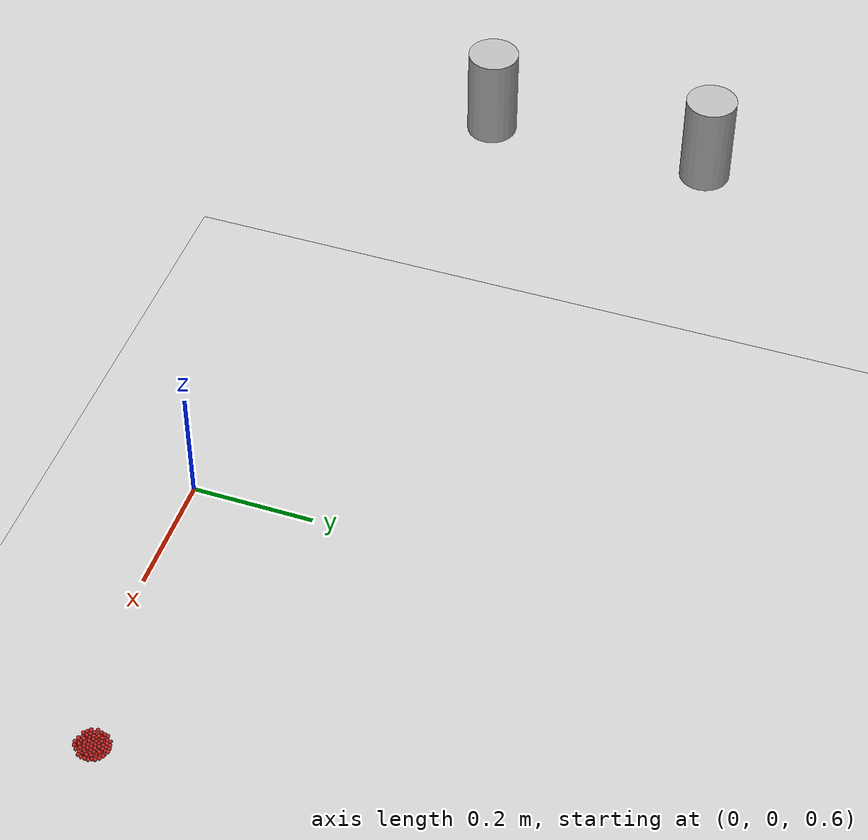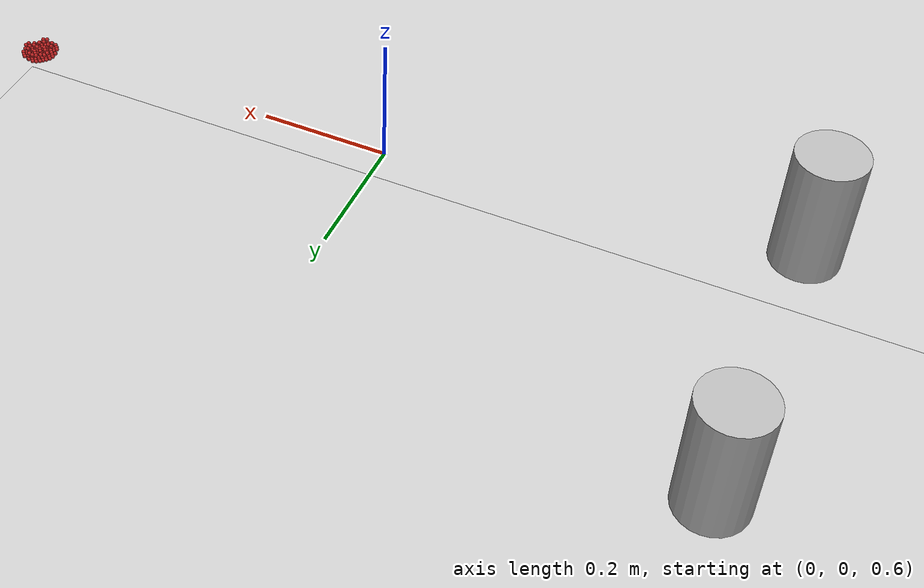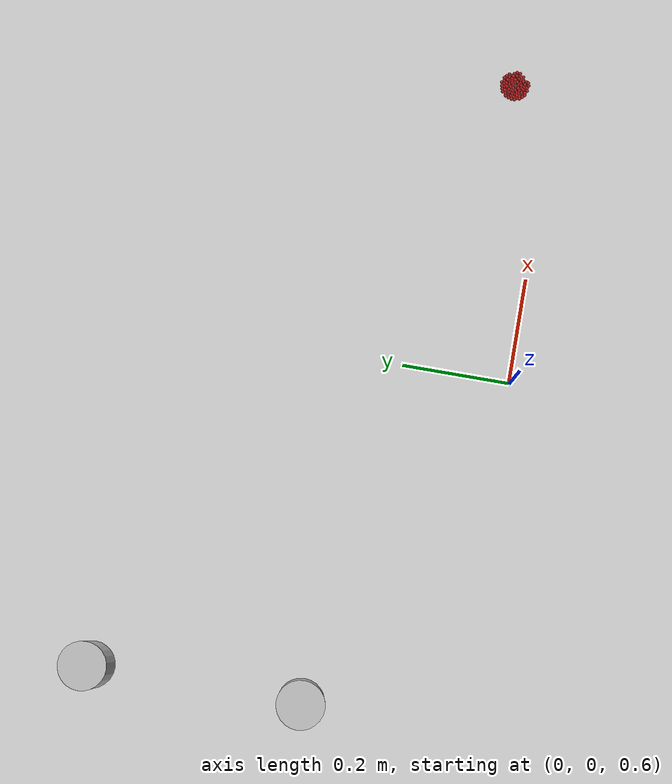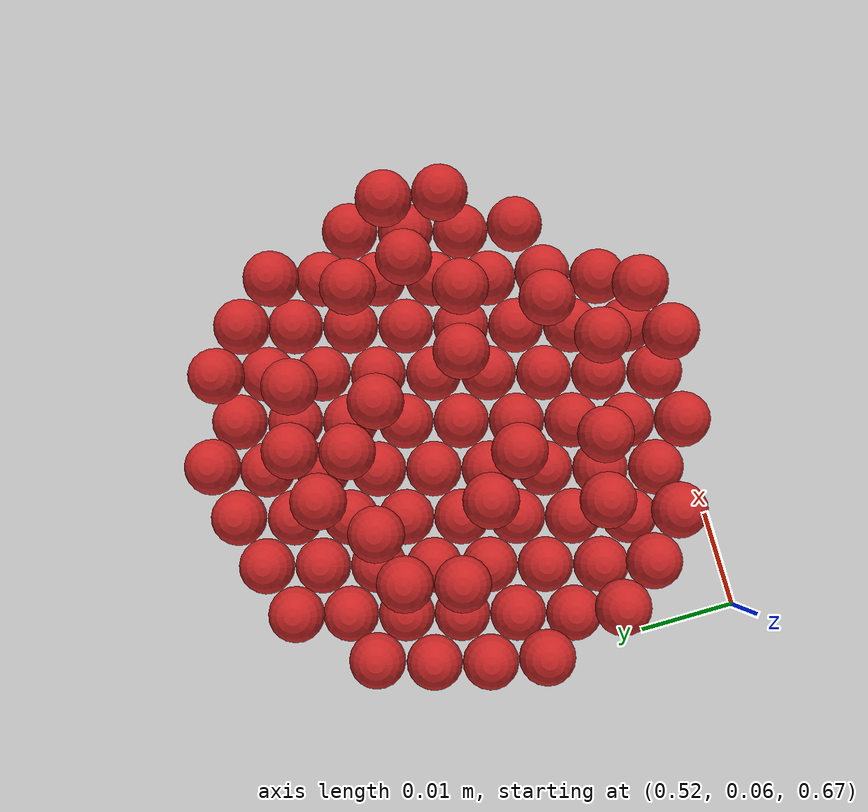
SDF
<sdf version="1.4">
 <world name="default">
  <physics type="ode">
   <gravity>0 0 -9.81</gravity>
   <ode>
    <solver><type>quick</type><iters>20</iters><sor>1</sor></solver>
    <constraints>
     <cfm>0</cfm>
     <erp>0.2</erp>
     <contact_max_correcting_vel>100</contact_max_correcting_vel>
     <contact_surface_layer>0</contact_surface_layer>
    </constraints>
   </ode>
   <real_time_update_rate>1000</real_time_update_rate>
   <max_step_size>0.001</max_step_size>
   <real_time_factor>1</real_time_factor>
  </physics>
  <light name="sun" type="directional">
   <pose>0 0 10 0 -0 0</pose>
   <diffuse>0.8 0.8 0.8 1</diffuse>
   <specular>0.2 0.2 0.2 1</specular>
   <attenuation>
    <range>1000</range>
    <constant>0.9</constant>
    <linear>0.01</linear>
    <quadratic>0.001</quadratic>
   </attenuation>
   <direction>-0.5 0.1 -0.9</direction>
  </light>
  <model name="ground_plane">
   <static>1</static>
   <link name="link">
    <collision name="collision">
     <geometry><plane><normal>0 0 1</normal><size>100 100</size></plane></geometry>
     <surface><friction><ode><mu>100</mu><mu2>50</mu2></ode></friction></surface>
    </collision>
    <visual name="visual">
     <cast_shadows>0</cast_shadows>
     <geometry><plane><normal>0 0 1</normal><size>100 100</size></plane></geometry>
     <material>
      <script><uri>file://media/materials/scripts/gazebo.material</uri><name>Gazebo/Grey</name></script>
     </material>
    </visual>
    <velocity_decay><linear>0</linear><angular>0</angular></velocity_decay>
   </link>
  </model>
  <scene><ambient>0.4 0.4 0.4 1</ambient><background>0.7 0.7 0.7 1</background><shadows>1</shadows></scene>
  <spherical_coordinates>
   <surface_model>EARTH_WGS84</surface_model>
   <latitude_deg>0</latitude_deg>
   <longitude_deg>0</longitude_deg>
   <elevation>0</elevation>
   <heading_deg>0</heading_deg>
  </spherical_coordinates>
  <model name="cocacola">
   <static>0</static>
   <link name="link">
    <inertial>
     <mass>0.25</mass>
     <inertia><ixx>0</ixx><ixy>0</ixy><ixz>0</ixz><iyy>0</iyy><iyz>0</iyz><izz>0</izz></inertia>
    </inertial>
    <collision name="collision">
     <pose>0 0 0.075 -3.14159 -0 0</pose>
     <geometry><cylinder><radius>0.04</radius><length>0.15</length></cylinder></geometry>
    </collision>
    <visual name="visual">
     <pose>0 0 0.075 -3.14159 -0 0</pose>
     <geometry><cylinder><radius>0.04</radius><length>0.15</length></cylinder></geometry>
     <material>
      <script>
       <uri>model://cocacola/material/scripts</uri>
       <uri>model://cocacola/material/textures</uri>
       <name>Custom/cocacola</name>
      </script>
     </material>
    </visual>
    <velocity_decay><linear>0</linear><angular>0</angular></velocity_decay>
   </link>
   <pose>-0.635135 0.281961 0.920008 9e-05 -0.000174 -0.00223</pose>
  </model>
  <model name="sprite">
   <static>0</static>
   <link name="link">
    <inertial>
     <mass>0.25</mass>
     <inertia><ixx>0</ixx><ixy>0</ixy><ixz>0</ixz><iyy>0</iyy><iyz>0</iyz><izz>0</izz></inertia>
    </inertial>
    <collision name="collision">
     <pose>0 0 0.075 -3.14159 -0 0</pose>
     <geometry><cylinder><radius>0.04</radius><length>0.15</length></cylinder></geometry>
    </collision>
    <visual name="visual">
     <pose>0 0 0.075 -3.14159 -0 0</pose>
     <geometry><cylinder><radius>0.04</radius><length>0.15</length></cylinder></geometry>
     <material>
      <script>
       <uri>model://sprite/material/scripts</uri>
       <uri>model://sprite/material/textures</uri>
       <name>Custom/sprite</name>
      </script>
     </material>
    </visual>
    <velocity_decay><linear>0</linear><angular>0</angular></velocity_decay>
   </link>
   <pose>-0.633912 0.639664 0.920008 0.000196 -7.7e-05 0.020234</pose>
  </model>
  <model name="sphere0">
   <pose>-0.002085 -0.000161 -0.026429 -0.000498 -0.00059 2.7e-05</pose>
   <link name="link">
    <pose>0.534545 0.067517 0.694885 0 -0 0</pose>
    <inertial>
     <mass>1e-08</mass>
     <inertia><ixx>4e-08</ixx><ixy>0</ixy><ixz>0</ixz><iyy>4e-08</iyy><iyz>0</iyz><izz>4e-08</izz></inertia>
    </inertial>
    <collision name="collision">
     <surface>
      <bounce><restitution_coefficient>0.5</restitution_coefficient><threshold>0</threshold></bounce>
      <contact><ode><kp>1e+08</kp><kd>1</kd></ode></contact>
      <friction><ode><mu>1e-06</mu><mu2>1e-06</mu2></ode></friction>
     </surface>
     <geometry><sphere><radius>0.003</radius></sphere></geometry>
    </collision>
    <visual name="visual">
     <geometry><sphere><radius>0.003</radius></sphere></geometry>
     <material>
      <script><uri>file://media/materials/scripts/gazebo.material</uri><name>Gazebo/Red</name></script>
     </material>
    </visual>
    <velocity_decay><linear>0</linear><angular>0</angular></velocity_decay>
   </link>
   <static>0</static>
  </model>
  <model name="sphere1">
   <pose>0.003203 0.003386 -0.026011 0.000162 -7.8e-05 1.65436e-24</pose>
   <link name="link">
    <pose>0.540545 0.067517 0.694885 0 -0 0</pose>
    <inertial>
     <mass>1e-08</mass>
     <inertia><ixx>4e-08</ixx><ixy>0</ixy><ixz>0</ixz><iyy>4e-08</iyy><iyz>0</iyz><izz>4e-08</izz></inertia>
    </inertial>
    <collision name="collision">
     <surface>
      <bounce><restitution_coefficient>0.5</restitution_coefficient><threshold>0</threshold></bounce>
      <contact><ode><kp>1e+08</kp><kd>1</kd></ode></contact>
      <friction><ode><mu>1e-06</mu><mu2>1e-06</mu2></ode></friction>
     </surface>
     <geometry><sphere><radius>0.003</radius></sphere></geometry>
    </collision>
    <visual name="visual">
     <geometry><sphere><radius>0.003</radius></sphere></geometry>
     <material>
      <script><uri>file://media/materials/scripts/gazebo.material</uri><name>Gazebo/Red</name></script>
     </material>
    </visual>
    <velocity_decay><linear>0</linear><angular>0</angular></velocity_decay>
   </link>
   <static>0</static>
  </model>
  <model name="sphere2">
   <pose>0.005686 -0.005185 -0.026004 0.000139 -0.000249 -1.8e-05</pose>
   <link name="link">
    <pose>0.546545 0.067517 0.694885 0 -0 0</pose>
    <inertial>
     <mass>1e-08</mass>
     <inertia><ixx>4e-08</ixx><ixy>0</ixy><ixz>0</ixz><iyy>4e-08</iyy><iyz>0</iyz><izz>4e-08</izz></inertia>
    </inertial>
    <collision name="collision">
     <surface>
      <bounce><restitution_coefficient>0.5</restitution_coefficient><threshold>0</threshold></bounce>
      <contact><ode><kp>1e+08</kp><kd>1</kd></ode></contact>
      <friction><ode><mu>1e-06</mu><mu2>1e-06</mu2></ode></friction>
     </surface>
     <geometry><sphere><radius>0.003</radius></sphere></geometry>
    </collision>
    <visual name="visual">
     <geometry><sphere><radius>0.003</radius></sphere></geometry>
     <material>
      <script><uri>file://media/materials/scripts/gazebo.material</uri><name>Gazebo/Red</name></script>
     </material>
    </visual>
    <velocity_decay><linear>0</linear><angular>0</angular></velocity_decay>
   </link>
   <static>0</static>
  </model>
  <model name="sphere3">
   <pose>0.017734 0.010482 -0.021147 -0.000144 0.000294 -0.000125</pose>
   <link name="link">
    <pose>0.552545 0.067517 0.694885 0 -0 0</pose>
    <inertial>
     <mass>1e-08</mass>
     <inertia><ixx>4e-08</ixx><ixy>0</ixy><ixz>0</ixz><iyy>4e-08</iyy><iyz>0</iyz><izz>4e-08</izz></inertia>
    </inertial>
    <collision name="collision">
     <surface>
      <bounce><restitution_coefficient>0.5</restitution_coefficient><threshold>0</threshold></bounce>
      <contact><ode><kp>1e+08</kp><kd>1</kd></ode></contact>
      <friction><ode><mu>1e-06</mu><mu2>1e-06</mu2></ode></friction>
     </surface>
     <geometry><sphere><radius>0.003</radius></sphere></geometry>
    </collision>
    <visual name="visual">
     <geometry><sphere><radius>0.003</radius></sphere></geometry>
     <material>
      <script><uri>file://media/materials/scripts/gazebo.material</uri><name>Gazebo/Red</name></script>
     </material>
    </visual>
    <velocity_decay><linear>0</linear><angular>0</angular></velocity_decay>
   </link>
   <static>0</static>
  </model>
  <model name="sphere4">
   <pose>-0.003405 0.010831 -0.026081 0.000968 -2.2e-05 0</pose>
   <link name="link">
    <pose>0.534545 0.073517 0.694885 0 -0 0</pose>
    <inertial>
     <mass>1e-08</mass>
     <inertia><ixx>4e-08</ixx><ixy>0</ixy><ixz>0</ixz><iyy>4e-08</iyy><iyz>0</iyz><izz>4e-08</izz></inertia>
    </inertial>
    <collision name="collision">
     <surface>
      <bounce><restitution_coefficient>0.5</restitution_coefficient><threshold>0</threshold></bounce>
      <contact><ode><kp>1e+08</kp><kd>1</kd></ode></contact>
      <friction><ode><mu>1e-06</mu><mu2>1e-06</mu2></ode></friction>
     </surface>
     <geometry><sphere><radius>0.003</radius></sphere></geometry>
    </collision>
    <visual name="visual">
     <geometry><sphere><radius>0.003</radius></sphere></geometry>
     <material>
      <script><uri>file://media/materials/scripts/gazebo.material</uri><name>Gazebo/Red</name></script>
     </material>
    </visual>
    <velocity_decay><linear>0</linear><angular>0</angular></velocity_decay>
   </link>
   <static>0</static>
  </model>
  <model name="sphere5">
   <pose>0.000769 0.007472 -0.026106 0.000181 -0.000287 -1.32349e-23</pose>
   <link name="link">
    <pose>0.540545 0.073517 0.694885 0 -0 0</pose>
    <inertial>
     <mass>1e-08</mass>
     <inertia><ixx>4e-08</ixx><ixy>0</ixy><ixz>0</ixz><iyy>4e-08</iyy><iyz>0</iyz><izz>4e-08</izz></inertia>
    </inertial>
    <collision name="collision">
     <surface>
      <bounce><restitution_coefficient>0.5</restitution_coefficient><threshold>0</threshold></bounce>
      <contact><ode><kp>1e+08</kp><kd>1</kd></ode></contact>
      <friction><ode><mu>1e-06</mu><mu2>1e-06</mu2></ode></friction>
     </surface>
     <geometry><sphere><radius>0.003</radius></sphere></geometry>
    </collision>
    <visual name="visual">
     <geometry><sphere><radius>0.003</radius></sphere></geometry>
     <material>
      <script><uri>file://media/materials/scripts/gazebo.material</uri><name>Gazebo/Red</name></script>
     </material>
    </visual>
    <velocity_decay><linear>0</linear><angular>0</angular></velocity_decay>
   </link>
   <static>0</static>
  </model>
  <model name="sphere6">
   <pose>0.016097 0.007825 -0.025996 0.000464 0.000126 0</pose>
   <link name="link">
    <pose>0.546545 0.073517 0.694885 0 -0 0</pose>
    <inertial>
     <mass>1e-08</mass>
     <inertia><ixx>4e-08</ixx><ixy>0</ixy><ixz>0</ixz><iyy>4e-08</iyy><iyz>0</iyz><izz>4e-08</izz></inertia>
    </inertial>
    <collision name="collision">
     <surface>
      <bounce><restitution_coefficient>0.5</restitution_coefficient><threshold>0</threshold></bounce>
      <contact><ode><kp>1e+08</kp><kd>1</kd></ode></contact>
      <friction><ode><mu>1e-06</mu><mu2>1e-06</mu2></ode></friction>
     </surface>
     <geometry><sphere><radius>0.003</radius></sphere></geometry>
    </collision>
    <visual name="visual">
     <geometry><sphere><radius>0.003</radius></sphere></geometry>
     <material>
      <script><uri>file://media/materials/scripts/gazebo.material</uri><name>Gazebo/Red</name></script>
     </material>
    </visual>
    <velocity_decay><linear>0</linear><angular>0</angular></velocity_decay>
   </link>
   <static>0</static>
  </model>
  <model name="sphere7">
   <pose>0.018692 0.010598 -0.02054 0.000226 0.000135 -8.8e-05</pose>
   <link name="link">
    <pose>0.552545 0.073517 0.694885 0 -0 0</pose>
    <inertial>
     <mass>1e-08</mass>
     <inertia><ixx>4e-08</ixx><ixy>0</ixy><ixz>0</ixz><iyy>4e-08</iyy><iyz>0</iyz><izz>4e-08</izz></inertia>
    </inertial>
    <collision name="collision">
     <surface>
      <bounce><restitution_coefficient>0.5</restitution_coefficient><threshold>0</threshold></bounce>
      <contact><ode><kp>1e+08</kp><kd>1</kd></ode></contact>
      <friction><ode><mu>1e-06</mu><mu2>1e-06</mu2></ode></friction>
     </surface>
     <geometry><sphere><radius>0.003</radius></sphere></geometry>
    </collision>
    <visual name="visual">
     <geometry><sphere><radius>0.003</radius></sphere></geometry>
     <material>
      <script><uri>file://media/materials/scripts/gazebo.material</uri><name>Gazebo/Red</name></script>
     </material>
    </visual>
    <velocity_decay><linear>0</linear><angular>0</angular></velocity_decay>
   </link>
   <static>0</static>
  </model>
  <model name="sphere8">
   <pose>-0.013819 0.001396 -0.023412 0.000246 -0.000644 -0.000271</pose>
   <link name="link">
    <pose>0.534545 0.079517 0.694885 0 -0 0</pose>
    <inertial>
     <mass>1e-08</mass>
     <inertia><ixx>4e-08</ixx><ixy>0</ixy><ixz>0</ixz><iyy>4e-08</iyy><iyz>0</iyz><izz>4e-08</izz></inertia>
    </inertial>
    <collision name="collision">
     <surface>
      <bounce><restitution_coefficient>0.5</restitution_coefficient><threshold>0</threshold></bounce>
      <contact><ode><kp>1e+08</kp><kd>1</kd></ode></contact>
      <friction><ode><mu>1e-06</mu><mu2>1e-06</mu2></ode></friction>
     </surface>
     <geometry><sphere><radius>0.003</radius></sphere></geometry>
    </collision>
    <visual name="visual">
     <geometry><sphere><radius>0.003</radius></sphere></geometry>
     <material>
      <script><uri>file://media/materials/scripts/gazebo.material</uri><name>Gazebo/Red</name></script>
     </material>
    </visual>
    <velocity_decay><linear>0</linear><angular>0</angular></velocity_decay>
   </link>
   <static>0</static>
  </model>
  <model name="sphere9">
   <pose>0.004028 0.012873 -0.026133 -4.2e-05 -0.000319 1.65436e-24</pose>
   <link name="link">
    <pose>0.540545 0.079517 0.694885 0 -0 0</pose>
    <inertial>
     <mass>1e-08</mass>
     <inertia><ixx>4e-08</ixx><ixy>0</ixy><ixz>0</ixz><iyy>4e-08</iyy><iyz>0</iyz><izz>4e-08</izz></inertia>
    </inertial>
    <collision name="collision">
     <surface>
      <bounce><restitution_coefficient>0.5</restitution_coefficient><threshold>0</threshold></bounce>
      <contact><ode><kp>1e+08</kp><kd>1</kd></ode></contact>
      <friction><ode><mu>1e-06</mu><mu2>1e-06</mu2></ode></friction>
     </surface>
     <geometry><sphere><radius>0.003</radius></sphere></geometry>
    </collision>
    <visual name="visual">
     <geometry><sphere><radius>0.003</radius></sphere></geometry>
     <material>
      <script><uri>file://media/materials/scripts/gazebo.material</uri><name>Gazebo/Red</name></script>
     </material>
    </visual>
    <velocity_decay><linear>0</linear><angular>0</angular></velocity_decay>
   </link>
   <static>0</static>
  </model>
  <model name="sphere10">
   <pose>0.006021 0.004342 -0.025845 6.4e-05 0.000215 0</pose>
   <link name="link">
    <pose>0.546545 0.079517 0.694885 0 -0 0</pose>
    <inertial>
     <mass>1e-08</mass>
     <inertia><ixx>4e-08</ixx><ixy>0</ixy><ixz>0</ixz><iyy>4e-08</iyy><iyz>0</iyz><izz>4e-08</izz></inertia>
    </inertial>
    <collision name="collision">
     <surface>
      <bounce><restitution_coefficient>0.5</restitution_coefficient><threshold>0</threshold></bounce>
      <contact><ode><kp>1e+08</kp><kd>1</kd></ode></contact>
      <friction><ode><mu>1e-06</mu><mu2>1e-06</mu2></ode></friction>
     </surface>
     <geometry><sphere><radius>0.003</radius></sphere></geometry>
    </collision>
    <visual name="visual">
     <geometry><sphere><radius>0.003</radius></sphere></geometry>
     <material>
      <script><uri>file://media/materials/scripts/gazebo.material</uri><name>Gazebo/Red</name></script>
     </material>
    </visual>
    <velocity_decay><linear>0</linear><angular>0</angular></velocity_decay>
   </link>
   <static>0</static>
  </model>
  <model name="sphere11">
   <pose>0.013849 0.017939 -0.022685 -9.7e-05 0.000891 0.000489</pose>
   <link name="link">
    <pose>0.552545 0.079517 0.694885 0 -0 0</pose>
    <inertial>
     <mass>1e-08</mass>
     <inertia><ixx>4e-08</ixx><ixy>0</ixy><ixz>0</ixz><iyy>4e-08</iyy><iyz>0</iyz><izz>4e-08</izz></inertia>
    </inertial>
    <collision name="collision">
     <surface>
      <bounce><restitution_coefficient>0.5</restitution_coefficient><threshold>0</threshold></bounce>
      <contact><ode><kp>1e+08</kp><kd>1</kd></ode></contact>
      <friction><ode><mu>1e-06</mu><mu2>1e-06</mu2></ode></friction>
     </surface>
     <geometry><sphere><radius>0.003</radius></sphere></geometry>
    </collision>
    <visual name="visual">
     <geometry><sphere><radius>0.003</radius></sphere></geometry>
     <material>
      <script><uri>file://media/materials/scripts/gazebo.material</uri><name>Gazebo/Red</name></script>
     </material>
    </visual>
    <velocity_decay><linear>0</linear><angular>0</angular></velocity_decay>
   </link>
   <static>0</static>
  </model>
  <model name="sphere12">
   <pose>-0.009416 0.012347 -0.024125 -0.000316 -0.000498 -0.000281</pose>
   <link name="link">
    <pose>0.534545 0.085517 0.694885 0 -0 0</pose>
    <inertial>
     <mass>1e-08</mass>
     <inertia><ixx>4e-08</ixx><ixy>0</ixy><ixz>0</ixz><iyy>4e-08</iyy><iyz>0</iyz><izz>4e-08</izz></inertia>
    </inertial>
    <collision name="collision">
     <surface>
      <bounce><restitution_coefficient>0.5</restitution_coefficient><threshold>0</threshold></bounce>
      <contact><ode><kp>1e+08</kp><kd>1</kd></ode></contact>
      <friction><ode><mu>1e-06</mu><mu2>1e-06</mu2></ode></friction>
     </surface>
     <geometry><sphere><radius>0.003</radius></sphere></geometry>
    </collision>
    <visual name="visual">
     <geometry><sphere><radius>0.003</radius></sphere></geometry>
     <material>
      <script><uri>file://media/materials/scripts/gazebo.material</uri><name>Gazebo/Red</name></script>
     </material>
    </visual>
    <velocity_decay><linear>0</linear><angular>0</angular></velocity_decay>
   </link>
   <static>0</static>
  </model>
  <model name="sphere13">
   <pose>-0.004499 0.015285 -0.025986 -0.000249 -0.000102 3.4e-05</pose>
   <link name="link">
    <pose>0.540545 0.085517 0.694885 0 -0 0</pose>
    <inertial>
     <mass>1e-08</mass>
     <inertia><ixx>4e-08</ixx><ixy>0</ixy><ixz>0</ixz><iyy>4e-08</iyy><iyz>0</iyz><izz>4e-08</izz></inertia>
    </inertial>
    <collision name="collision">
     <surface>
      <bounce><restitution_coefficient>0.5</restitution_coefficient><threshold>0</threshold></bounce>
      <contact><ode><kp>1e+08</kp><kd>1</kd></ode></contact>
      <friction><ode><mu>1e-06</mu><mu2>1e-06</mu2></ode></friction>
     </surface>
     <geometry><sphere><radius>0.003</radius></sphere></geometry>
    </collision>
    <visual name="visual">
     <geometry><sphere><radius>0.003</radius></sphere></geometry>
     <material>
      <script><uri>file://media/materials/scripts/gazebo.material</uri><name>Gazebo/Red</name></script>
     </material>
    </visual>
    <velocity_decay><linear>0</linear><angular>0</angular></velocity_decay>
   </link>
   <static>0</static>
  </model>
  <model name="sphere14">
   <pose>0.002752 0.023182 -0.023402 -0.000726 1.1e-05 -8.3e-05</pose>
   <link name="link">
    <pose>0.546545 0.085517 0.694885 0 -0 0</pose>
    <inertial>
     <mass>1e-08</mass>
     <inertia><ixx>4e-08</ixx><ixy>0</ixy><ixz>0</ixz><iyy>4e-08</iyy><iyz>0</iyz><izz>4e-08</izz></inertia>
    </inertial>
    <collision name="collision">
     <surface>
      <bounce><restitution_coefficient>0.5</restitution_coefficient><threshold>0</threshold></bounce>
      <contact><ode><kp>1e+08</kp><kd>1</kd></ode></contact>
      <friction><ode><mu>1e-06</mu><mu2>1e-06</mu2></ode></friction>
     </surface>
     <geometry><sphere><radius>0.003</radius></sphere></geometry>
    </collision>
    <visual name="visual">
     <geometry><sphere><radius>0.003</radius></sphere></geometry>
     <material>
      <script><uri>file://media/materials/scripts/gazebo.material</uri><name>Gazebo/Red</name></script>
     </material>
    </visual>
    <velocity_decay><linear>0</linear><angular>0</angular></velocity_decay>
   </link>
   <static>0</static>
  </model>
  <model name="sphere15">
   <pose>0.010319 0.016833 -0.023531 1.2e-05 8.4e-05 -0.000222</pose>
   <link name="link">
    <pose>0.552545 0.085517 0.694885 0 -0 0</pose>
    <inertial>
     <mass>1e-08</mass>
     <inertia><ixx>4e-08</ixx><ixy>0</ixy><ixz>0</ixz><iyy>4e-08</iyy><iyz>0</iyz><izz>4e-08</izz></inertia>
    </inertial>
    <collision name="collision">
     <surface>
      <bounce><restitution_coefficient>0.5</restitution_coefficient><threshold>0</threshold></bounce>
      <contact><ode><kp>1e+08</kp><kd>1</kd></ode></contact>
      <friction><ode><mu>1e-06</mu><mu2>1e-06</mu2></ode></friction>
     </surface>
     <geometry><sphere><radius>0.003</radius></sphere></geometry>
    </collision>
    <visual name="visual">
     <geometry><sphere><radius>0.003</radius></sphere></geometry>
     <material>
      <script><uri>file://media/materials/scripts/gazebo.material</uri><name>Gazebo/Red</name></script>
     </material>
    </visual>
    <velocity_decay><linear>0</linear><angular>0</angular></velocity_decay>
   </link>
   <static>0</static>
  </model>
  <model name="sphere16">
   <pose>0.00165 -0.003881 -0.031895 0.00021 0.000134 -3.1e-05</pose>
   <link name="link">
    <pose>0.534545 0.067517 0.700885 0 -0 0</pose>
    <inertial>
     <mass>1e-08</mass>
     <inertia><ixx>4e-08</ixx><ixy>0</ixy><ixz>0</ixz><iyy>4e-08</iyy><iyz>0</iyz><izz>4e-08</izz></inertia>
    </inertial>
    <collision name="collision">
     <surface>
      <bounce><restitution_coefficient>0.5</restitution_coefficient><threshold>0</threshold></bounce>
      <contact><ode><kp>1e+08</kp><kd>1</kd></ode></contact>
      <friction><ode><mu>1e-06</mu><mu2>1e-06</mu2></ode></friction>
     </surface>
     <geometry><sphere><radius>0.003</radius></sphere></geometry>
    </collision>
    <visual name="visual">
     <geometry><sphere><radius>0.003</radius></sphere></geometry>
     <material>
      <script><uri>file://media/materials/scripts/gazebo.material</uri><name>Gazebo/Red</name></script>
     </material>
    </visual>
    <velocity_decay><linear>0</linear><angular>0</angular></velocity_decay>
   </link>
   <static>0</static>
  </model>
  <model name="sphere17">
   <pose>0.000987 -0.002211 -0.03166 0.000405 0.000742 -2e-06</pose>
   <link name="link">
    <pose>0.540545 0.067517 0.700885 0 -0 0</pose>
    <inertial>
     <mass>1e-08</mass>
     <inertia><ixx>4e-08</ixx><ixy>0</ixy><ixz>0</ixz><iyy>4e-08</iyy><iyz>0</iyz><izz>4e-08</izz></inertia>
    </inertial>
    <collision name="collision">
     <surface>
      <bounce><restitution_coefficient>0.5</restitution_coefficient><threshold>0</threshold></bounce>
      <contact><ode><kp>1e+08</kp><kd>1</kd></ode></contact>
      <friction><ode><mu>1e-06</mu><mu2>1e-06</mu2></ode></friction>
     </surface>
     <geometry><sphere><radius>0.003</radius></sphere></geometry>
    </collision>
    <visual name="visual">
     <geometry><sphere><radius>0.003</radius></sphere></geometry>
     <material>
      <script><uri>file://media/materials/scripts/gazebo.material</uri><name>Gazebo/Red</name></script>
     </material>
    </visual>
    <velocity_decay><linear>0</linear><angular>0</angular></velocity_decay>
   </link>
   <static>0</static>
  </model>
  <model name="sphere18">
   <pose>-0.000304 -0.00684 -0.031547 -0.000162 8e-06 -5.6e-05</pose>
   <link name="link">
    <pose>0.546545 0.067517 0.700885 0 -0 0</pose>
    <inertial>
     <mass>1e-08</mass>
     <inertia><ixx>4e-08</ixx><ixy>0</ixy><ixz>0</ixz><iyy>4e-08</iyy><iyz>0</iyz><izz>4e-08</izz></inertia>
    </inertial>
    <collision name="collision">
     <surface>
      <bounce><restitution_coefficient>0.5</restitution_coefficient><threshold>0</threshold></bounce>
      <contact><ode><kp>1e+08</kp><kd>1</kd></ode></contact>
      <friction><ode><mu>1e-06</mu><mu2>1e-06</mu2></ode></friction>
     </surface>
     <geometry><sphere><radius>0.003</radius></sphere></geometry>
    </collision>
    <visual name="visual">
     <geometry><sphere><radius>0.003</radius></sphere></geometry>
     <material>
      <script><uri>file://media/materials/scripts/gazebo.material</uri><name>Gazebo/Red</name></script>
     </material>
    </visual>
    <velocity_decay><linear>0</linear><angular>0</angular></velocity_decay>
   </link>
   <static>0</static>
  </model>
  <model name="sphere19">
   <pose>0.002918 -0.007158 -0.027279 -6e-06 -7.4e-05 1.7e-05</pose>
   <link name="link">
    <pose>0.552545 0.067517 0.700885 0 -0 0</pose>
    <inertial>
     <mass>1e-08</mass>
     <inertia><ixx>4e-08</ixx><ixy>0</ixy><ixz>0</ixz><iyy>4e-08</iyy><iyz>0</iyz><izz>4e-08</izz></inertia>
    </inertial>
    <collision name="collision">
     <surface>
      <bounce><restitution_coefficient>0.5</restitution_coefficient><threshold>0</threshold></bounce>
      <contact><ode><kp>1e+08</kp><kd>1</kd></ode></contact>
      <friction><ode><mu>1e-06</mu><mu2>1e-06</mu2></ode></friction>
     </surface>
     <geometry><sphere><radius>0.003</radius></sphere></geometry>
    </collision>
    <visual name="visual">
     <geometry><sphere><radius>0.003</radius></sphere></geometry>
     <material>
      <script><uri>file://media/materials/scripts/gazebo.material</uri><name>Gazebo/Red</name></script>
     </material>
    </visual>
    <velocity_decay><linear>0</linear><angular>0</angular></velocity_decay>
   </link>
   <static>0</static>
  </model>
  <model name="sphere20">
   <pose>-0.006531 -0.001627 -0.032068 -0.000328 -0.000208 1e-05</pose>
   <link name="link">
    <pose>0.534545 0.073517 0.700885 0 -0 0</pose>
    <inertial>
     <mass>1e-08</mass>
     <inertia><ixx>4e-08</ixx><ixy>0</ixy><ixz>0</ixz><iyy>4e-08</iyy><iyz>0</iyz><izz>4e-08</izz></inertia>
    </inertial>
    <collision name="collision">
     <surface>
      <bounce><restitution_coefficient>0.5</restitution_coefficient><threshold>0</threshold></bounce>
      <contact><ode><kp>1e+08</kp><kd>1</kd></ode></contact>
      <friction><ode><mu>1e-06</mu><mu2>1e-06</mu2></ode></friction>
     </surface>
     <geometry><sphere><radius>0.003</radius></sphere></geometry>
    </collision>
    <visual name="visual">
     <geometry><sphere><radius>0.003</radius></sphere></geometry>
     <material>
      <script><uri>file://media/materials/scripts/gazebo.material</uri><name>Gazebo/Red</name></script>
     </material>
    </visual>
    <velocity_decay><linear>0</linear><angular>0</angular></velocity_decay>
   </link>
   <static>0</static>
  </model>
  <model name="sphere21">
   <pose>-0.005341 0.006202 -0.031902 0.000493 0.000149 0</pose>
   <link name="link">
    <pose>0.540545 0.073517 0.700885 0 -0 0</pose>
    <inertial>
     <mass>1e-08</mass>
     <inertia><ixx>4e-08</ixx><ixy>0</ixy><ixz>0</ixz><iyy>4e-08</iyy><iyz>0</iyz><izz>4e-08</izz></inertia>
    </inertial>
    <collision name="collision">
     <surface>
      <bounce><restitution_coefficient>0.5</restitution_coefficient><threshold>0</threshold></bounce>
      <contact><ode><kp>1e+08</kp><kd>1</kd></ode></contact>
      <friction><ode><mu>1e-06</mu><mu2>1e-06</mu2></ode></friction>
     </surface>
     <geometry><sphere><radius>0.003</radius></sphere></geometry>
    </collision>
    <visual name="visual">
     <geometry><sphere><radius>0.003</radius></sphere></geometry>
     <material>
      <script><uri>file://media/materials/scripts/gazebo.material</uri><name>Gazebo/Red</name></script>
     </material>
    </visual>
    <velocity_decay><linear>0</linear><angular>0</angular></velocity_decay>
   </link>
   <static>0</static>
  </model>
  <model name="sphere22">
   <pose>0.008789 0.000331 -0.032001 0.00011 -2.9e-05 -4.1359e-25</pose>
   <link name="link">
    <pose>0.546545 0.073517 0.700885 0 -0 0</pose>
    <inertial>
     <mass>1e-08</mass>
     <inertia><ixx>4e-08</ixx><ixy>0</ixy><ixz>0</ixz><iyy>4e-08</iyy><iyz>0</iyz><izz>4e-08</izz></inertia>
    </inertial>
    <collision name="collision">
     <surface>
      <bounce><restitution_coefficient>0.5</restitution_coefficient><threshold>0</threshold></bounce>
      <contact><ode><kp>1e+08</kp><kd>1</kd></ode></contact>
      <friction><ode><mu>1e-06</mu><mu2>1e-06</mu2></ode></friction>
     </surface>
     <geometry><sphere><radius>0.003</radius></sphere></geometry>
    </collision>
    <visual name="visual">
     <geometry><sphere><radius>0.003</radius></sphere></geometry>
     <material>
      <script><uri>file://media/materials/scripts/gazebo.material</uri><name>Gazebo/Red</name></script>
     </material>
    </visual>
    <velocity_decay><linear>0</linear><angular>0</angular></velocity_decay>
   </link>
   <static>0</static>
  </model>
  <model name="sphere23">
   <pose>0.005376 -0.009689 -0.031397 3.4e-05 2.3e-05 1.5e-05</pose>
   <link name="link">
    <pose>0.552545 0.073517 0.700885 0 -0 0</pose>
    <inertial>
     <mass>1e-08</mass>
     <inertia><ixx>4e-08</ixx><ixy>0</ixy><ixz>0</ixz><iyy>4e-08</iyy><iyz>0</iyz><izz>4e-08</izz></inertia>
    </inertial>
    <collision name="collision">
     <surface>
      <bounce><restitution_coefficient>0.5</restitution_coefficient><threshold>0</threshold></bounce>
      <contact><ode><kp>1e+08</kp><kd>1</kd></ode></contact>
      <friction><ode><mu>1e-06</mu><mu2>1e-06</mu2></ode></friction>
     </surface>
     <geometry><sphere><radius>0.003</radius></sphere></geometry>
    </collision>
    <visual name="visual">
     <geometry><sphere><radius>0.003</radius></sphere></geometry>
     <material>
      <script><uri>file://media/materials/scripts/gazebo.material</uri><name>Gazebo/Red</name></script>
     </material>
    </visual>
    <velocity_decay><linear>0</linear><angular>0</angular></velocity_decay>
   </link>
   <static>0</static>
  </model>
  <model name="sphere24">
   <pose>-0.010826 -0.003438 -0.031703 -0.000501 -4.9e-05 -1.3e-05</pose>
   <link name="link">
    <pose>0.534545 0.079517 0.700885 0 -0 0</pose>
    <inertial>
     <mass>1e-08</mass>
     <inertia><ixx>4e-08</ixx><ixy>0</ixy><ixz>0</ixz><iyy>4e-08</iyy><iyz>0</iyz><izz>4e-08</izz></inertia>
    </inertial>
    <collision name="collision">
     <surface>
      <bounce><restitution_coefficient>0.5</restitution_coefficient><threshold>0</threshold></bounce>
      <contact><ode><kp>1e+08</kp><kd>1</kd></ode></contact>
      <friction><ode><mu>1e-06</mu><mu2>1e-06</mu2></ode></friction>
     </surface>
     <geometry><sphere><radius>0.003</radius></sphere></geometry>
    </collision>
    <visual name="visual">
     <geometry><sphere><radius>0.003</radius></sphere></geometry>
     <material>
      <script><uri>file://media/materials/scripts/gazebo.material</uri><name>Gazebo/Red</name></script>
     </material>
    </visual>
    <velocity_decay><linear>0</linear><angular>0</angular></velocity_decay>
   </link>
   <static>0</static>
  </model>
  <model name="sphere25">
   <pose>-0.002157 0.011226 -0.031824 -0.000268 0.000216 -6.61745e-24</pose>
   <link name="link">
    <pose>0.540545 0.079517 0.700885 0 -0 0</pose>
    <inertial>
     <mass>1e-08</mass>
     <inertia><ixx>4e-08</ixx><ixy>0</ixy><ixz>0</ixz><iyy>4e-08</iyy><iyz>0</iyz><izz>4e-08</izz></inertia>
    </inertial>
    <collision name="collision">
     <surface>
      <bounce><restitution_coefficient>0.5</restitution_coefficient><threshold>0</threshold></bounce>
      <contact><ode><kp>1e+08</kp><kd>1</kd></ode></contact>
      <friction><ode><mu>1e-06</mu><mu2>1e-06</mu2></ode></friction>
     </surface>
     <geometry><sphere><radius>0.003</radius></sphere></geometry>
    </collision>
    <visual name="visual">
     <geometry><sphere><radius>0.003</radius></sphere></geometry>
     <material>
      <script><uri>file://media/materials/scripts/gazebo.material</uri><name>Gazebo/Red</name></script>
     </material>
    </visual>
    <velocity_decay><linear>0</linear><angular>0</angular></velocity_decay>
   </link>
   <static>0</static>
  </model>
  <model name="sphere26">
   <pose>0.007331 0.010245 -0.031635 0.000214 0.000681 0</pose>
   <link name="link">
    <pose>0.546545 0.079517 0.700885 0 -0 0</pose>
    <inertial>
     <mass>1e-08</mass>
     <inertia><ixx>4e-08</ixx><ixy>0</ixy><ixz>0</ixz><iyy>4e-08</iyy><iyz>0</iyz><izz>4e-08</izz></inertia>
    </inertial>
    <collision name="collision">
     <surface>
      <bounce><restitution_coefficient>0.5</restitution_coefficient><threshold>0</threshold></bounce>
      <contact><ode><kp>1e+08</kp><kd>1</kd></ode></contact>
      <friction><ode><mu>1e-06</mu><mu2>1e-06</mu2></ode></friction>
     </surface>
     <geometry><sphere><radius>0.003</radius></sphere></geometry>
    </collision>
    <visual name="visual">
     <geometry><sphere><radius>0.003</radius></sphere></geometry>
     <material>
      <script><uri>file://media/materials/scripts/gazebo.material</uri><name>Gazebo/Red</name></script>
     </material>
    </visual>
    <velocity_decay><linear>0</linear><angular>0</angular></velocity_decay>
   </link>
   <static>0</static>
  </model>
  <model name="sphere27">
   <pose>0.01716 0.008794 -0.030247 0.000286 0.000306 0.000388</pose>
   <link name="link">
    <pose>0.552545 0.079517 0.700885 0 -0 0</pose>
    <inertial>
     <mass>1e-08</mass>
     <inertia><ixx>4e-08</ixx><ixy>0</ixy><ixz>0</ixz><iyy>4e-08</iyy><iyz>0</iyz><izz>4e-08</izz></inertia>
    </inertial>
    <collision name="collision">
     <surface>
      <bounce><restitution_coefficient>0.5</restitution_coefficient><threshold>0</threshold></bounce>
      <contact><ode><kp>1e+08</kp><kd>1</kd></ode></contact>
      <friction><ode><mu>1e-06</mu><mu2>1e-06</mu2></ode></friction>
     </surface>
     <geometry><sphere><radius>0.003</radius></sphere></geometry>
    </collision>
    <visual name="visual">
     <geometry><sphere><radius>0.003</radius></sphere></geometry>
     <material>
      <script><uri>file://media/materials/scripts/gazebo.material</uri><name>Gazebo/Red</name></script>
     </material>
    </visual>
    <velocity_decay><linear>0</linear><angular>0</angular></velocity_decay>
   </link>
   <static>0</static>
  </model>
  <model name="sphere28">
   <pose>-0.01331 0.000935 -0.030878 -3.3e-05 -1.5e-05 -4.5e-05</pose>
   <link name="link">
    <pose>0.534545 0.085517 0.700885 0 -0 0</pose>
    <inertial>
     <mass>1e-08</mass>
     <inertia><ixx>4e-08</ixx><ixy>0</ixy><ixz>0</ixz><iyy>4e-08</iyy><iyz>0</iyz><izz>4e-08</izz></inertia>
    </inertial>
    <collision name="collision">
     <surface>
      <bounce><restitution_coefficient>0.5</restitution_coefficient><threshold>0</threshold></bounce>
      <contact><ode><kp>1e+08</kp><kd>1</kd></ode></contact>
      <friction><ode><mu>1e-06</mu><mu2>1e-06</mu2></ode></friction>
     </surface>
     <geometry><sphere><radius>0.003</radius></sphere></geometry>
    </collision>
    <visual name="visual">
     <geometry><sphere><radius>0.003</radius></sphere></geometry>
     <material>
      <script><uri>file://media/materials/scripts/gazebo.material</uri><name>Gazebo/Red</name></script>
     </material>
    </visual>
    <velocity_decay><linear>0</linear><angular>0</angular></velocity_decay>
   </link>
   <static>0</static>
  </model>
  <model name="sphere29">
   <pose>-0.011882 0.008384 -0.032079 0.000289 -0.000157 5.8e-05</pose>
   <link name="link">
    <pose>0.540545 0.085517 0.700885 0 -0 0</pose>
    <inertial>
     <mass>1e-08</mass>
     <inertia><ixx>4e-08</ixx><ixy>0</ixy><ixz>0</ixz><iyy>4e-08</iyy><iyz>0</iyz><izz>4e-08</izz></inertia>
    </inertial>
    <collision name="collision">
     <surface>
      <bounce><restitution_coefficient>0.5</restitution_coefficient><threshold>0</threshold></bounce>
      <contact><ode><kp>1e+08</kp><kd>1</kd></ode></contact>
      <friction><ode><mu>1e-06</mu><mu2>1e-06</mu2></ode></friction>
     </surface>
     <geometry><sphere><radius>0.003</radius></sphere></geometry>
    </collision>
    <visual name="visual">
     <geometry><sphere><radius>0.003</radius></sphere></geometry>
     <material>
      <script><uri>file://media/materials/scripts/gazebo.material</uri><name>Gazebo/Red</name></script>
     </material>
    </visual>
    <velocity_decay><linear>0</linear><angular>0</angular></velocity_decay>
   </link>
   <static>0</static>
  </model>
  <model name="sphere30">
   <pose>-0.004652 0.016917 -0.032024 -8e-05 -0.00017 -1.8e-05</pose>
   <link name="link">
    <pose>0.546545 0.085517 0.700885 0 -0 0</pose>
    <inertial>
     <mass>1e-08</mass>
     <inertia><ixx>4e-08</ixx><ixy>0</ixy><ixz>0</ixz><iyy>4e-08</iyy><iyz>0</iyz><izz>4e-08</izz></inertia>
    </inertial>
    <collision name="collision">
     <surface>
      <bounce><restitution_coefficient>0.5</restitution_coefficient><threshold>0</threshold></bounce>
      <contact><ode><kp>1e+08</kp><kd>1</kd></ode></contact>
      <friction><ode><mu>1e-06</mu><mu2>1e-06</mu2></ode></friction>
     </surface>
     <geometry><sphere><radius>0.003</radius></sphere></geometry>
    </collision>
    <visual name="visual">
     <geometry><sphere><radius>0.003</radius></sphere></geometry>
     <material>
      <script><uri>file://media/materials/scripts/gazebo.material</uri><name>Gazebo/Red</name></script>
     </material>
    </visual>
    <velocity_decay><linear>0</linear><angular>0</angular></velocity_decay>
   </link>
   <static>0</static>
  </model>
  <model name="sphere31">
   <pose>0.009113 0.011439 -0.032021 0.0001 0.000183 -3e-06</pose>
   <link name="link">
    <pose>0.552545 0.085517 0.700885 0 -0 0</pose>
    <inertial>
     <mass>1e-08</mass>
     <inertia><ixx>4e-08</ixx><ixy>0</ixy><ixz>0</ixz><iyy>4e-08</iyy><iyz>0</iyz><izz>4e-08</izz></inertia>
    </inertial>
    <collision name="collision">
     <surface>
      <bounce><restitution_coefficient>0.5</restitution_coefficient><threshold>0</threshold></bounce>
      <contact><ode><kp>1e+08</kp><kd>1</kd></ode></contact>
      <friction><ode><mu>1e-06</mu><mu2>1e-06</mu2></ode></friction>
     </surface>
     <geometry><sphere><radius>0.003</radius></sphere></geometry>
    </collision>
    <visual name="visual">
     <geometry><sphere><radius>0.003</radius></sphere></geometry>
     <material>
      <script><uri>file://media/materials/scripts/gazebo.material</uri><name>Gazebo/Red</name></script>
     </material>
    </visual>
    <velocity_decay><linear>0</linear><angular>0</angular></velocity_decay>
   </link>
   <static>0</static>
  </model>
  <model name="sphere32">
   <pose>-0.007673 -0.000603 -0.035175 -1e-06 3.1e-05 1.2e-05</pose>
   <link name="link">
    <pose>0.534545 0.067517 0.706885 0 -0 0</pose>
    <inertial>
     <mass>1e-08</mass>
     <inertia><ixx>4e-08</ixx><ixy>0</ixy><ixz>0</ixz><iyy>4e-08</iyy><iyz>0</iyz><izz>4e-08</izz></inertia>
    </inertial>
    <collision name="collision">
     <surface>
      <bounce><restitution_coefficient>0.5</restitution_coefficient><threshold>0</threshold></bounce>
      <contact><ode><kp>1e+08</kp><kd>1</kd></ode></contact>
      <friction><ode><mu>1e-06</mu><mu2>1e-06</mu2></ode></friction>
     </surface>
     <geometry><sphere><radius>0.003</radius></sphere></geometry>
    </collision>
    <visual name="visual">
     <geometry><sphere><radius>0.003</radius></sphere></geometry>
     <material>
      <script><uri>file://media/materials/scripts/gazebo.material</uri><name>Gazebo/Red</name></script>
     </material>
    </visual>
    <velocity_decay><linear>0</linear><angular>0</angular></velocity_decay>
   </link>
   <static>0</static>
  </model>
  <model name="sphere33">
   <pose>0.007444 -0.000948 -0.038104 6.8e-05 -0.000172 -1.65436e-24</pose>
   <link name="link">
    <pose>0.540545 0.067517 0.706885 0 -0 0</pose>
    <inertial>
     <mass>1e-08</mass>
     <inertia><ixx>4e-08</ixx><ixy>0</ixy><ixz>0</ixz><iyy>4e-08</iyy><iyz>0</iyz><izz>4e-08</izz></inertia>
    </inertial>
    <collision name="collision">
     <surface>
      <bounce><restitution_coefficient>0.5</restitution_coefficient><threshold>0</threshold></bounce>
      <contact><ode><kp>1e+08</kp><kd>1</kd></ode></contact>
      <friction><ode><mu>1e-06</mu><mu2>1e-06</mu2></ode></friction>
     </surface>
     <geometry><sphere><radius>0.003</radius></sphere></geometry>
    </collision>
    <visual name="visual">
     <geometry><sphere><radius>0.003</radius></sphere></geometry>
     <material>
      <script><uri>file://media/materials/scripts/gazebo.material</uri><name>Gazebo/Red</name></script>
     </material>
    </visual>
    <velocity_decay><linear>0</linear><angular>0</angular></velocity_decay>
   </link>
   <static>0</static>
  </model>
  <model name="sphere34">
   <pose>0.003111 -0.008665 -0.033055 0.000181 -2.5e-05 6.3e-05</pose>
   <link name="link">
    <pose>0.546545 0.067517 0.706885 0 -0 0</pose>
    <inertial>
     <mass>1e-08</mass>
     <inertia><ixx>4e-08</ixx><ixy>0</ixy><ixz>0</ixz><iyy>4e-08</iyy><iyz>0</iyz><izz>4e-08</izz></inertia>
    </inertial>
    <collision name="collision">
     <surface>
      <bounce><restitution_coefficient>0.5</restitution_coefficient><threshold>0</threshold></bounce>
      <contact><ode><kp>1e+08</kp><kd>1</kd></ode></contact>
      <friction><ode><mu>1e-06</mu><mu2>1e-06</mu2></ode></friction>
     </surface>
     <geometry><sphere><radius>0.003</radius></sphere></geometry>
    </collision>
    <visual name="visual">
     <geometry><sphere><radius>0.003</radius></sphere></geometry>
     <material>
      <script><uri>file://media/materials/scripts/gazebo.material</uri><name>Gazebo/Red</name></script>
     </material>
    </visual>
    <velocity_decay><linear>0</linear><angular>0</angular></velocity_decay>
   </link>
   <static>0</static>
  </model>
  <model name="sphere35">
   <pose>0.012338 0.016035 -0.033068 0 -0 0</pose>
   <link name="link">
    <pose>0.552545 0.067517 0.706885 0 -0 0</pose>
    <inertial>
     <mass>1e-08</mass>
     <inertia><ixx>4e-08</ixx><ixy>0</ixy><ixz>0</ixz><iyy>4e-08</iyy><iyz>0</iyz><izz>4e-08</izz></inertia>
    </inertial>
    <collision name="collision">
     <surface>
      <bounce><restitution_coefficient>0.5</restitution_coefficient><threshold>0</threshold></bounce>
      <contact><ode><kp>1e+08</kp><kd>1</kd></ode></contact>
      <friction><ode><mu>1e-06</mu><mu2>1e-06</mu2></ode></friction>
     </surface>
     <geometry><sphere><radius>0.003</radius></sphere></geometry>
    </collision>
    <visual name="visual">
     <geometry><sphere><radius>0.003</radius></sphere></geometry>
     <material>
      <script><uri>file://media/materials/scripts/gazebo.material</uri><name>Gazebo/Red</name></script>
     </material>
    </visual>
    <velocity_decay><linear>0</linear><angular>0</angular></velocity_decay>
   </link>
   <static>0</static>
  </model>
  <model name="sphere36">
   <pose>-0.004272 0.01348 -0.033075 0 -0 0</pose>
   <link name="link">
    <pose>0.534545 0.073517 0.706885 0 -0 0</pose>
    <inertial>
     <mass>1e-08</mass>
     <inertia><ixx>4e-08</ixx><ixy>0</ixy><ixz>0</ixz><iyy>4e-08</iyy><iyz>0</iyz><izz>4e-08</izz></inertia>
    </inertial>
    <collision name="collision">
     <surface>
      <bounce><restitution_coefficient>0.5</restitution_coefficient><threshold>0</threshold></bounce>
      <contact><ode><kp>1e+08</kp><kd>1</kd></ode></contact>
      <friction><ode><mu>1e-06</mu><mu2>1e-06</mu2></ode></friction>
     </surface>
     <geometry><sphere><radius>0.003</radius></sphere></geometry>
    </collision>
    <visual name="visual">
     <geometry><sphere><radius>0.003</radius></sphere></geometry>
     <material>
      <script><uri>file://media/materials/scripts/gazebo.material</uri><name>Gazebo/Red</name></script>
     </material>
    </visual>
    <velocity_decay><linear>0</linear><angular>0</angular></velocity_decay>
   </link>
   <static>0</static>
  </model>
  <model name="sphere37">
   <pose>0.010604 0.004582 -0.037971 5.5e-05 -4.4e-05 -4.1359e-25</pose>
   <link name="link">
    <pose>0.540545 0.073517 0.706885 0 -0 0</pose>
    <inertial>
     <mass>1e-08</mass>
     <inertia><ixx>4e-08</ixx><ixy>0</ixy><ixz>0</ixz><iyy>4e-08</iyy><iyz>0</iyz><izz>4e-08</izz></inertia>
    </inertial>
    <collision name="collision">
     <surface>
      <bounce><restitution_coefficient>0.5</restitution_coefficient><threshold>0</threshold></bounce>
      <contact><ode><kp>1e+08</kp><kd>1</kd></ode></contact>
      <friction><ode><mu>1e-06</mu><mu2>1e-06</mu2></ode></friction>
     </surface>
     <geometry><sphere><radius>0.003</radius></sphere></geometry>
    </collision>
    <visual name="visual">
     <geometry><sphere><radius>0.003</radius></sphere></geometry>
     <material>
      <script><uri>file://media/materials/scripts/gazebo.material</uri><name>Gazebo/Red</name></script>
     </material>
    </visual>
    <velocity_decay><linear>0</linear><angular>0</angular></velocity_decay>
   </link>
   <static>0</static>
  </model>
  <model name="sphere38">
   <pose>0.010422 0.00613 -0.03807 0.000175 -6.8e-05 -3.30872e-24</pose>
   <link name="link">
    <pose>0.546545 0.073517 0.706885 0 -0 0</pose>
    <inertial>
     <mass>1e-08</mass>
     <inertia><ixx>4e-08</ixx><ixy>0</ixy><ixz>0</ixz><iyy>4e-08</iyy><iyz>0</iyz><izz>4e-08</izz></inertia>
    </inertial>
    <collision name="collision">
     <surface>
      <bounce><restitution_coefficient>0.5</restitution_coefficient><threshold>0</threshold></bounce>
      <contact><ode><kp>1e+08</kp><kd>1</kd></ode></contact>
      <friction><ode><mu>1e-06</mu><mu2>1e-06</mu2></ode></friction>
     </surface>
     <geometry><sphere><radius>0.003</radius></sphere></geometry>
    </collision>
    <visual name="visual">
     <geometry><sphere><radius>0.003</radius></sphere></geometry>
     <material>
      <script><uri>file://media/materials/scripts/gazebo.material</uri><name>Gazebo/Red</name></script>
     </material>
    </visual>
    <velocity_decay><linear>0</linear><angular>0</angular></velocity_decay>
   </link>
   <static>0</static>
  </model>
  <model name="sphere39">
   <pose>0.016184 0.008938 -0.037876 -0.000186 -0.000299 -0.000136</pose>
   <link name="link">
    <pose>0.552545 0.073517 0.706885 0 -0 0</pose>
    <inertial>
     <mass>1e-08</mass>
     <inertia><ixx>4e-08</ixx><ixy>0</ixy><ixz>0</ixz><iyy>4e-08</iyy><iyz>0</iyz><izz>4e-08</izz></inertia>
    </inertial>
    <collision name="collision">
     <surface>
      <bounce><restitution_coefficient>0.5</restitution_coefficient><threshold>0</threshold></bounce>
      <contact><ode><kp>1e+08</kp><kd>1</kd></ode></contact>
      <friction><ode><mu>1e-06</mu><mu2>1e-06</mu2></ode></friction>
     </surface>
     <geometry><sphere><radius>0.003</radius></sphere></geometry>
    </collision>
    <visual name="visual">
     <geometry><sphere><radius>0.003</radius></sphere></geometry>
     <material>
      <script><uri>file://media/materials/scripts/gazebo.material</uri><name>Gazebo/Red</name></script>
     </material>
    </visual>
    <velocity_decay><linear>0</linear><angular>0</angular></velocity_decay>
   </link>
   <static>0</static>
  </model>
  <model name="sphere40">
   <pose>-0.007537 0.008574 -0.038036 0.000139 -0.000116 -5.4e-05</pose>
   <link name="link">
    <pose>0.534545 0.079517 0.706885 0 -0 0</pose>
    <inertial>
     <mass>1e-08</mass>
     <inertia><ixx>4e-08</ixx><ixy>0</ixy><ixz>0</ixz><iyy>4e-08</iyy><iyz>0</iyz><izz>4e-08</izz></inertia>
    </inertial>
    <collision name="collision">
     <surface>
      <bounce><restitution_coefficient>0.5</restitution_coefficient><threshold>0</threshold></bounce>
      <contact><ode><kp>1e+08</kp><kd>1</kd></ode></contact>
      <friction><ode><mu>1e-06</mu><mu2>1e-06</mu2></ode></friction>
     </surface>
     <geometry><sphere><radius>0.003</radius></sphere></geometry>
    </collision>
    <visual name="visual">
     <geometry><sphere><radius>0.003</radius></sphere></geometry>
     <material>
      <script><uri>file://media/materials/scripts/gazebo.material</uri><name>Gazebo/Red</name></script>
     </material>
    </visual>
    <velocity_decay><linear>0</linear><angular>0</angular></velocity_decay>
   </link>
   <static>0</static>
  </model>
  <model name="sphere41">
   <pose>-0.000329 0.017163 -0.03798 -3.9e-05 -8.3e-05 0</pose>
   <link name="link">
    <pose>0.540545 0.079517 0.706885 0 -0 0</pose>
    <inertial>
     <mass>1e-08</mass>
     <inertia><ixx>4e-08</ixx><ixy>0</ixy><ixz>0</ixz><iyy>4e-08</iyy><iyz>0</iyz><izz>4e-08</izz></inertia>
    </inertial>
    <collision name="collision">
     <surface>
      <bounce><restitution_coefficient>0.5</restitution_coefficient><threshold>0</threshold></bounce>
      <contact><ode><kp>1e+08</kp><kd>1</kd></ode></contact>
      <friction><ode><mu>1e-06</mu><mu2>1e-06</mu2></ode></friction>
     </surface>
     <geometry><sphere><radius>0.003</radius></sphere></geometry>
    </collision>
    <visual name="visual">
     <geometry><sphere><radius>0.003</radius></sphere></geometry>
     <material>
      <script><uri>file://media/materials/scripts/gazebo.material</uri><name>Gazebo/Red</name></script>
     </material>
    </visual>
    <velocity_decay><linear>0</linear><angular>0</angular></velocity_decay>
   </link>
   <static>0</static>
  </model>
  <model name="sphere42">
   <pose>-0.000703 0.018667 -0.037872 -2e-05 0.00017 4.1359e-25</pose>
   <link name="link">
    <pose>0.546545 0.079517 0.706885 0 -0 0</pose>
    <inertial>
     <mass>1e-08</mass>
     <inertia><ixx>4e-08</ixx><ixy>0</ixy><ixz>0</ixz><iyy>4e-08</iyy><iyz>0</iyz><izz>4e-08</izz></inertia>
    </inertial>
    <collision name="collision">
     <surface>
      <bounce><restitution_coefficient>0.5</restitution_coefficient><threshold>0</threshold></bounce>
      <contact><ode><kp>1e+08</kp><kd>1</kd></ode></contact>
      <friction><ode><mu>1e-06</mu><mu2>1e-06</mu2></ode></friction>
     </surface>
     <geometry><sphere><radius>0.003</radius></sphere></geometry>
    </collision>
    <visual name="visual">
     <geometry><sphere><radius>0.003</radius></sphere></geometry>
     <material>
      <script><uri>file://media/materials/scripts/gazebo.material</uri><name>Gazebo/Red</name></script>
     </material>
    </visual>
    <velocity_decay><linear>0</linear><angular>0</angular></velocity_decay>
   </link>
   <static>0</static>
  </model>
  <model name="sphere43">
   <pose>0.013343 0.01334 -0.037932 0.000344 0.000123 -4.5e-05</pose>
   <link name="link">
    <pose>0.552545 0.079517 0.706885 0 -0 0</pose>
    <inertial>
     <mass>1e-08</mass>
     <inertia><ixx>4e-08</ixx><ixy>0</ixy><ixz>0</ixz><iyy>4e-08</iyy><iyz>0</iyz><izz>4e-08</izz></inertia>
    </inertial>
    <collision name="collision">
     <surface>
      <bounce><restitution_coefficient>0.5</restitution_coefficient><threshold>0</threshold></bounce>
      <contact><ode><kp>1e+08</kp><kd>1</kd></ode></contact>
      <friction><ode><mu>1e-06</mu><mu2>1e-06</mu2></ode></friction>
     </surface>
     <geometry><sphere><radius>0.003</radius></sphere></geometry>
    </collision>
    <visual name="visual">
     <geometry><sphere><radius>0.003</radius></sphere></geometry>
     <material>
      <script><uri>file://media/materials/scripts/gazebo.material</uri><name>Gazebo/Red</name></script>
     </material>
    </visual>
    <velocity_decay><linear>0</linear><angular>0</angular></velocity_decay>
   </link>
   <static>0</static>
  </model>
  <model name="sphere44">
   <pose>-0.002358 0.019445 -0.036284 -0.000405 -0.000583 -0.000692</pose>
   <link name="link">
    <pose>0.534545 0.085517 0.706885 0 -0 0</pose>
    <inertial>
     <mass>1e-08</mass>
     <inertia><ixx>4e-08</ixx><ixy>0</ixy><ixz>0</ixz><iyy>4e-08</iyy><iyz>0</iyz><izz>4e-08</izz></inertia>
    </inertial>
    <collision name="collision">
     <surface>
      <bounce><restitution_coefficient>0.5</restitution_coefficient><threshold>0</threshold></bounce>
      <contact><ode><kp>1e+08</kp><kd>1</kd></ode></contact>
      <friction><ode><mu>1e-06</mu><mu2>1e-06</mu2></ode></friction>
     </surface>
     <geometry><sphere><radius>0.003</radius></sphere></geometry>
    </collision>
    <visual name="visual">
     <geometry><sphere><radius>0.003</radius></sphere></geometry>
     <material>
      <script><uri>file://media/materials/scripts/gazebo.material</uri><name>Gazebo/Red</name></script>
     </material>
    </visual>
    <velocity_decay><linear>0</linear><angular>0</angular></velocity_decay>
   </link>
   <static>0</static>
  </model>
  <model name="sphere45">
   <pose>-0.002799 0.021104 -0.037337 -0.000127 -0.000224 1e-05</pose>
   <link name="link">
    <pose>0.540545 0.085517 0.706885 0 -0 0</pose>
    <inertial>
     <mass>1e-08</mass>
     <inertia><ixx>4e-08</ixx><ixy>0</ixy><ixz>0</ixz><iyy>4e-08</iyy><iyz>0</iyz><izz>4e-08</izz></inertia>
    </inertial>
    <collision name="collision">
     <surface>
      <bounce><restitution_coefficient>0.5</restitution_coefficient><threshold>0</threshold></bounce>
      <contact><ode><kp>1e+08</kp><kd>1</kd></ode></contact>
      <friction><ode><mu>1e-06</mu><mu2>1e-06</mu2></ode></friction>
     </surface>
     <geometry><sphere><radius>0.003</radius></sphere></geometry>
    </collision>
    <visual name="visual">
     <geometry><sphere><radius>0.003</radius></sphere></geometry>
     <material>
      <script><uri>file://media/materials/scripts/gazebo.material</uri><name>Gazebo/Red</name></script>
     </material>
    </visual>
    <velocity_decay><linear>0</linear><angular>0</angular></velocity_decay>
   </link>
   <static>0</static>
  </model>
  <model name="sphere46">
   <pose>-0.003276 0.022634 -0.037028 -0.00018 0.000177 -0.000153</pose>
   <link name="link">
    <pose>0.546545 0.085517 0.706885 0 -0 0</pose>
    <inertial>
     <mass>1e-08</mass>
     <inertia><ixx>4e-08</ixx><ixy>0</ixy><ixz>0</ixz><iyy>4e-08</iyy><iyz>0</iyz><izz>4e-08</izz></inertia>
    </inertial>
    <collision name="collision">
     <surface>
      <bounce><restitution_coefficient>0.5</restitution_coefficient><threshold>0</threshold></bounce>
      <contact><ode><kp>1e+08</kp><kd>1</kd></ode></contact>
      <friction><ode><mu>1e-06</mu><mu2>1e-06</mu2></ode></friction>
     </surface>
     <geometry><sphere><radius>0.003</radius></sphere></geometry>
    </collision>
    <visual name="visual">
     <geometry><sphere><radius>0.003</radius></sphere></geometry>
     <material>
      <script><uri>file://media/materials/scripts/gazebo.material</uri><name>Gazebo/Red</name></script>
     </material>
    </visual>
    <velocity_decay><linear>0</linear><angular>0</angular></velocity_decay>
   </link>
   <static>0</static>
  </model>
  <model name="sphere47">
   <pose>0.005965 0.020591 -0.034751 7.5e-05 -5.3e-05 9.5e-05</pose>
   <link name="link">
    <pose>0.552545 0.085517 0.706885 0 -0 0</pose>
    <inertial>
     <mass>1e-08</mass>
     <inertia><ixx>4e-08</ixx><ixy>0</ixy><ixz>0</ixz><iyy>4e-08</iyy><iyz>0</iyz><izz>4e-08</izz></inertia>
    </inertial>
    <collision name="collision">
     <surface>
      <bounce><restitution_coefficient>0.5</restitution_coefficient><threshold>0</threshold></bounce>
      <contact><ode><kp>1e+08</kp><kd>1</kd></ode></contact>
      <friction><ode><mu>1e-06</mu><mu2>1e-06</mu2></ode></friction>
     </surface>
     <geometry><sphere><radius>0.003</radius></sphere></geometry>
    </collision>
    <visual name="visual">
     <geometry><sphere><radius>0.003</radius></sphere></geometry>
     <material>
      <script><uri>file://media/materials/scripts/gazebo.material</uri><name>Gazebo/Red</name></script>
     </material>
    </visual>
    <velocity_decay><linear>0</linear><angular>0</angular></velocity_decay>
   </link>
   <static>0</static>
  </model>
  <model name="sphere48">
   <pose>-0.003327 -0.004383 -0.040555 3.4e-05 0.000126 -0.000348</pose>
   <link name="link">
    <pose>0.534545 0.067517 0.712885 0 -0 0</pose>
    <inertial>
     <mass>1e-08</mass>
     <inertia><ixx>4e-08</ixx><ixy>0</ixy><ixz>0</ixz><iyy>4e-08</iyy><iyz>0</iyz><izz>4e-08</izz></inertia>
    </inertial>
    <collision name="collision">
     <surface>
      <bounce><restitution_coefficient>0.5</restitution_coefficient><threshold>0</threshold></bounce>
      <contact><ode><kp>1e+08</kp><kd>1</kd></ode></contact>
      <friction><ode><mu>1e-06</mu><mu2>1e-06</mu2></ode></friction>
     </surface>
     <geometry><sphere><radius>0.003</radius></sphere></geometry>
    </collision>
    <visual name="visual">
     <geometry><sphere><radius>0.003</radius></sphere></geometry>
     <material>
      <script><uri>file://media/materials/scripts/gazebo.material</uri><name>Gazebo/Red</name></script>
     </material>
    </visual>
    <velocity_decay><linear>0</linear><angular>0</angular></velocity_decay>
   </link>
   <static>0</static>
  </model>
  <model name="sphere49">
   <pose>-0.002203 0.001489 -0.044404 -0.000408 -0.000683 0</pose>
   <link name="link">
    <pose>0.540545 0.067517 0.712885 0 -0 0</pose>
    <inertial>
     <mass>1e-08</mass>
     <inertia><ixx>4e-08</ixx><ixy>0</ixy><ixz>0</ixz><iyy>4e-08</iyy><iyz>0</iyz><izz>4e-08</izz></inertia>
    </inertial>
    <collision name="collision">
     <surface>
      <bounce><restitution_coefficient>0.5</restitution_coefficient><threshold>0</threshold></bounce>
      <contact><ode><kp>1e+08</kp><kd>1</kd></ode></contact>
      <friction><ode><mu>1e-06</mu><mu2>1e-06</mu2></ode></friction>
     </surface>
     <geometry><sphere><radius>0.003</radius></sphere></geometry>
    </collision>
    <visual name="visual">
     <geometry><sphere><radius>0.003</radius></sphere></geometry>
     <material>
      <script><uri>file://media/materials/scripts/gazebo.material</uri><name>Gazebo/Red</name></script>
     </material>
    </visual>
    <velocity_decay><linear>0</linear><angular>0</angular></velocity_decay>
   </link>
   <static>0</static>
  </model>
  <model name="sphere50">
   <pose>-0.006032 -0.007887 -0.041972 6.4e-05 -5.5e-05 0.000121</pose>
   <link name="link">
    <pose>0.546545 0.067517 0.712885 0 -0 0</pose>
    <inertial>
     <mass>1e-08</mass>
     <inertia><ixx>4e-08</ixx><ixy>0</ixy><ixz>0</ixz><iyy>4e-08</iyy><iyz>0</iyz><izz>4e-08</izz></inertia>
    </inertial>
    <collision name="collision">
     <surface>
      <bounce><restitution_coefficient>0.5</restitution_coefficient><threshold>0</threshold></bounce>
      <contact><ode><kp>1e+08</kp><kd>1</kd></ode></contact>
      <friction><ode><mu>1e-06</mu><mu2>1e-06</mu2></ode></friction>
     </surface>
     <geometry><sphere><radius>0.003</radius></sphere></geometry>
    </collision>
    <visual name="visual">
     <geometry><sphere><radius>0.003</radius></sphere></geometry>
     <material>
      <script><uri>file://media/materials/scripts/gazebo.material</uri><name>Gazebo/Red</name></script>
     </material>
    </visual>
    <velocity_decay><linear>0</linear><angular>0</angular></velocity_decay>
   </link>
   <static>0</static>
  </model>
  <model name="sphere51">
   <pose>0.007858 0.00201 -0.044313 0.000305 -0.000319 4.8e-05</pose>
   <link name="link">
    <pose>0.552545 0.067517 0.712885 0 -0 0</pose>
    <inertial>
     <mass>1e-08</mass>
     <inertia><ixx>4e-08</ixx><ixy>0</ixy><ixz>0</ixz><iyy>4e-08</iyy><iyz>0</iyz><izz>4e-08</izz></inertia>
    </inertial>
    <collision name="collision">
     <surface>
      <bounce><restitution_coefficient>0.5</restitution_coefficient><threshold>0</threshold></bounce>
      <contact><ode><kp>1e+08</kp><kd>1</kd></ode></contact>
      <friction><ode><mu>1e-06</mu><mu2>1e-06</mu2></ode></friction>
     </surface>
     <geometry><sphere><radius>0.003</radius></sphere></geometry>
    </collision>
    <visual name="visual">
     <geometry><sphere><radius>0.003</radius></sphere></geometry>
     <material>
      <script><uri>file://media/materials/scripts/gazebo.material</uri><name>Gazebo/Red</name></script>
     </material>
    </visual>
    <velocity_decay><linear>0</linear><angular>0</angular></velocity_decay>
   </link>
   <static>0</static>
  </model>
  <model name="sphere52">
   <pose>-0.004991 0.004128 -0.044055 -0.00036 -8.8e-05 0</pose>
   <link name="link">
    <pose>0.534545 0.073517 0.712885 0 -0 0</pose>
    <inertial>
     <mass>1e-08</mass>
     <inertia><ixx>4e-08</ixx><ixy>0</ixy><ixz>0</ixz><iyy>4e-08</iyy><iyz>0</iyz><izz>4e-08</izz></inertia>
    </inertial>
    <collision name="collision">
     <surface>
      <bounce><restitution_coefficient>0.5</restitution_coefficient><threshold>0</threshold></bounce>
      <contact><ode><kp>1e+08</kp><kd>1</kd></ode></contact>
      <friction><ode><mu>1e-06</mu><mu2>1e-06</mu2></ode></friction>
     </surface>
     <geometry><sphere><radius>0.003</radius></sphere></geometry>
    </collision>
    <visual name="visual">
     <geometry><sphere><radius>0.003</radius></sphere></geometry>
     <material>
      <script><uri>file://media/materials/scripts/gazebo.material</uri><name>Gazebo/Red</name></script>
     </material>
    </visual>
    <velocity_decay><linear>0</linear><angular>0</angular></velocity_decay>
   </link>
   <static>0</static>
  </model>
  <model name="sphere53">
   <pose>-0.000935 0.001504 -0.044057 -8.1e-05 -0.000158 0</pose>
   <link name="link">
    <pose>0.540545 0.073517 0.712885 0 -0 0</pose>
    <inertial>
     <mass>1e-08</mass>
     <inertia><ixx>4e-08</ixx><ixy>0</ixy><ixz>0</ixz><iyy>4e-08</iyy><iyz>0</iyz><izz>4e-08</izz></inertia>
    </inertial>
    <collision name="collision">
     <surface>
      <bounce><restitution_coefficient>0.5</restitution_coefficient><threshold>0</threshold></bounce>
      <contact><ode><kp>1e+08</kp><kd>1</kd></ode></contact>
      <friction><ode><mu>1e-06</mu><mu2>1e-06</mu2></ode></friction>
     </surface>
     <geometry><sphere><radius>0.003</radius></sphere></geometry>
    </collision>
    <visual name="visual">
     <geometry><sphere><radius>0.003</radius></sphere></geometry>
     <material>
      <script><uri>file://media/materials/scripts/gazebo.material</uri><name>Gazebo/Red</name></script>
     </material>
    </visual>
    <velocity_decay><linear>0</linear><angular>0</angular></velocity_decay>
   </link>
   <static>0</static>
  </model>
  <model name="sphere54">
   <pose>0.00758 -0.005335 -0.04442 0.000262 -0.000609 0</pose>
   <link name="link">
    <pose>0.546545 0.073517 0.712885 0 -0 0</pose>
    <inertial>
     <mass>1e-08</mass>
     <inertia><ixx>4e-08</ixx><ixy>0</ixy><ixz>0</ixz><iyy>4e-08</iyy><iyz>0</iyz><izz>4e-08</izz></inertia>
    </inertial>
    <collision name="collision">
     <surface>
      <bounce><restitution_coefficient>0.5</restitution_coefficient><threshold>0</threshold></bounce>
      <contact><ode><kp>1e+08</kp><kd>1</kd></ode></contact>
      <friction><ode><mu>1e-06</mu><mu2>1e-06</mu2></ode></friction>
     </surface>
     <geometry><sphere><radius>0.003</radius></sphere></geometry>
    </collision>
    <visual name="visual">
     <geometry><sphere><radius>0.003</radius></sphere></geometry>
     <material>
      <script><uri>file://media/materials/scripts/gazebo.material</uri><name>Gazebo/Red</name></script>
     </material>
    </visual>
    <velocity_decay><linear>0</linear><angular>0</angular></velocity_decay>
   </link>
   <static>0</static>
  </model>
  <model name="sphere55">
   <pose>0.014522 0.002924 -0.044013 -0.000484 -0.000203 -8.9e-05</pose>
   <link name="link">
    <pose>0.552545 0.073517 0.712885 0 -0 0</pose>
    <inertial>
     <mass>1e-08</mass>
     <inertia><ixx>4e-08</ixx><ixy>0</ixy><ixz>0</ixz><iyy>4e-08</iyy><iyz>0</iyz><izz>4e-08</izz></inertia>
    </inertial>
    <collision name="collision">
     <surface>
      <bounce><restitution_coefficient>0.5</restitution_coefficient><threshold>0</threshold></bounce>
      <contact><ode><kp>1e+08</kp><kd>1</kd></ode></contact>
      <friction><ode><mu>1e-06</mu><mu2>1e-06</mu2></ode></friction>
     </surface>
     <geometry><sphere><radius>0.003</radius></sphere></geometry>
    </collision>
    <visual name="visual">
     <geometry><sphere><radius>0.003</radius></sphere></geometry>
     <material>
      <script><uri>file://media/materials/scripts/gazebo.material</uri><name>Gazebo/Red</name></script>
     </material>
    </visual>
    <velocity_decay><linear>0</linear><angular>0</angular></velocity_decay>
   </link>
   <static>0</static>
  </model>
  <model name="sphere56">
   <pose>-0.011176 -0.007659 -0.04041 0.000178 -0.000255 -0.000354</pose>
   <link name="link">
    <pose>0.534545 0.079517 0.712885 0 -0 0</pose>
    <inertial>
     <mass>1e-08</mass>
     <inertia><ixx>4e-08</ixx><ixy>0</ixy><ixz>0</ixz><iyy>4e-08</iyy><iyz>0</iyz><izz>4e-08</izz></inertia>
    </inertial>
    <collision name="collision">
     <surface>
      <bounce><restitution_coefficient>0.5</restitution_coefficient><threshold>0</threshold></bounce>
      <contact><ode><kp>1e+08</kp><kd>1</kd></ode></contact>
      <friction><ode><mu>1e-06</mu><mu2>1e-06</mu2></ode></friction>
     </surface>
     <geometry><sphere><radius>0.003</radius></sphere></geometry>
    </collision>
    <visual name="visual">
     <geometry><sphere><radius>0.003</radius></sphere></geometry>
     <material>
      <script><uri>file://media/materials/scripts/gazebo.material</uri><name>Gazebo/Red</name></script>
     </material>
    </visual>
    <velocity_decay><linear>0</linear><angular>0</angular></velocity_decay>
   </link>
   <static>0</static>
  </model>
  <model name="sphere57">
   <pose>0.008039 0.008551 -0.043964 -8.1e-05 -6e-05 -8.27181e-25</pose>
   <link name="link">
    <pose>0.540545 0.079517 0.712885 0 -0 0</pose>
    <inertial>
     <mass>1e-08</mass>
     <inertia><ixx>4e-08</ixx><ixy>0</ixy><ixz>0</ixz><iyy>4e-08</iyy><iyz>0</iyz><izz>4e-08</izz></inertia>
    </inertial>
    <collision name="collision">
     <surface>
      <bounce><restitution_coefficient>0.5</restitution_coefficient><threshold>0</threshold></bounce>
      <contact><ode><kp>1e+08</kp><kd>1</kd></ode></contact>
      <friction><ode><mu>1e-06</mu><mu2>1e-06</mu2></ode></friction>
     </surface>
     <geometry><sphere><radius>0.003</radius></sphere></geometry>
    </collision>
    <visual name="visual">
     <geometry><sphere><radius>0.003</radius></sphere></geometry>
     <material>
      <script><uri>file://media/materials/scripts/gazebo.material</uri><name>Gazebo/Red</name></script>
     </material>
    </visual>
    <velocity_decay><linear>0</linear><angular>0</angular></velocity_decay>
   </link>
   <static>0</static>
  </model>
  <model name="sphere58">
   <pose>0.003733 0.014275 -0.044015 -0.00016 -0.00016 3.30872e-24</pose>
   <link name="link">
    <pose>0.546545 0.079517 0.712885 0 -0 0</pose>
    <inertial>
     <mass>1e-08</mass>
     <inertia><ixx>4e-08</ixx><ixy>0</ixy><ixz>0</ixz><iyy>4e-08</iyy><iyz>0</iyz><izz>4e-08</izz></inertia>
    </inertial>
    <collision name="collision">
     <surface>
      <bounce><restitution_coefficient>0.5</restitution_coefficient><threshold>0</threshold></bounce>
      <contact><ode><kp>1e+08</kp><kd>1</kd></ode></contact>
      <friction><ode><mu>1e-06</mu><mu2>1e-06</mu2></ode></friction>
     </surface>
     <geometry><sphere><radius>0.003</radius></sphere></geometry>
    </collision>
    <visual name="visual">
     <geometry><sphere><radius>0.003</radius></sphere></geometry>
     <material>
      <script><uri>file://media/materials/scripts/gazebo.material</uri><name>Gazebo/Red</name></script>
     </material>
    </visual>
    <velocity_decay><linear>0</linear><angular>0</angular></velocity_decay>
   </link>
   <static>0</static>
  </model>
  <model name="sphere59">
   <pose>0.007684 0.011347 -0.044025 -0.000319 -8.8e-05 3.30872e-24</pose>
   <link name="link">
    <pose>0.552545 0.079517 0.712885 0 -0 0</pose>
    <inertial>
     <mass>1e-08</mass>
     <inertia><ixx>4e-08</ixx><ixy>0</ixy><ixz>0</ixz><iyy>4e-08</iyy><iyz>0</iyz><izz>4e-08</izz></inertia>
    </inertial>
    <collision name="collision">
     <surface>
      <bounce><restitution_coefficient>0.5</restitution_coefficient><threshold>0</threshold></bounce>
      <contact><ode><kp>1e+08</kp><kd>1</kd></ode></contact>
      <friction><ode><mu>1e-06</mu><mu2>1e-06</mu2></ode></friction>
     </surface>
     <geometry><sphere><radius>0.003</radius></sphere></geometry>
    </collision>
    <visual name="visual">
     <geometry><sphere><radius>0.003</radius></sphere></geometry>
     <material>
      <script><uri>file://media/materials/scripts/gazebo.material</uri><name>Gazebo/Red</name></script>
     </material>
    </visual>
    <velocity_decay><linear>0</linear><angular>0</angular></velocity_decay>
   </link>
   <static>0</static>
  </model>
  <model name="sphere60">
   <pose>-0.011586 0.006716 -0.043314 -0.000112 -0.000256 -0.000143</pose>
   <link name="link">
    <pose>0.534545 0.085517 0.712885 0 -0 0</pose>
    <inertial>
     <mass>1e-08</mass>
     <inertia><ixx>4e-08</ixx><ixy>0</ixy><ixz>0</ixz><iyy>4e-08</iyy><iyz>0</iyz><izz>4e-08</izz></inertia>
    </inertial>
    <collision name="collision">
     <surface>
      <bounce><restitution_coefficient>0.5</restitution_coefficient><threshold>0</threshold></bounce>
      <contact><ode><kp>1e+08</kp><kd>1</kd></ode></contact>
      <friction><ode><mu>1e-06</mu><mu2>1e-06</mu2></ode></friction>
     </surface>
     <geometry><sphere><radius>0.003</radius></sphere></geometry>
    </collision>
    <visual name="visual">
     <geometry><sphere><radius>0.003</radius></sphere></geometry>
     <material>
      <script><uri>file://media/materials/scripts/gazebo.material</uri><name>Gazebo/Red</name></script>
     </material>
    </visual>
    <velocity_decay><linear>0</linear><angular>0</angular></velocity_decay>
   </link>
   <static>0</static>
  </model>
  <model name="sphere61">
   <pose>-0.010466 0.013946 -0.044035 -4.1e-05 0.000117 3.2e-05</pose>
   <link name="link">
    <pose>0.540545 0.085517 0.712885 0 -0 0</pose>
    <inertial>
     <mass>1e-08</mass>
     <inertia><ixx>4e-08</ixx><ixy>0</ixy><ixz>0</ixz><iyy>4e-08</iyy><iyz>0</iyz><izz>4e-08</izz></inertia>
    </inertial>
    <collision name="collision">
     <surface>
      <bounce><restitution_coefficient>0.5</restitution_coefficient><threshold>0</threshold></bounce>
      <contact><ode><kp>1e+08</kp><kd>1</kd></ode></contact>
      <friction><ode><mu>1e-06</mu><mu2>1e-06</mu2></ode></friction>
     </surface>
     <geometry><sphere><radius>0.003</radius></sphere></geometry>
    </collision>
    <visual name="visual">
     <geometry><sphere><radius>0.003</radius></sphere></geometry>
     <material>
      <script><uri>file://media/materials/scripts/gazebo.material</uri><name>Gazebo/Red</name></script>
     </material>
    </visual>
    <velocity_decay><linear>0</linear><angular>0</angular></velocity_decay>
   </link>
   <static>0</static>
  </model>
  <model name="sphere62">
   <pose>0.001558 0.018281 -0.044327 -0.000231 -0.000729 2.3e-05</pose>
   <link name="link">
    <pose>0.546545 0.085517 0.712885 0 -0 0</pose>
    <inertial>
     <mass>1e-08</mass>
     <inertia><ixx>4e-08</ixx><ixy>0</ixy><ixz>0</ixz><iyy>4e-08</iyy><iyz>0</iyz><izz>4e-08</izz></inertia>
    </inertial>
    <collision name="collision">
     <surface>
      <bounce><restitution_coefficient>0.5</restitution_coefficient><threshold>0</threshold></bounce>
      <contact><ode><kp>1e+08</kp><kd>1</kd></ode></contact>
      <friction><ode><mu>1e-06</mu><mu2>1e-06</mu2></ode></friction>
     </surface>
     <geometry><sphere><radius>0.003</radius></sphere></geometry>
    </collision>
    <visual name="visual">
     <geometry><sphere><radius>0.003</radius></sphere></geometry>
     <material>
      <script><uri>file://media/materials/scripts/gazebo.material</uri><name>Gazebo/Red</name></script>
     </material>
    </visual>
    <velocity_decay><linear>0</linear><angular>0</angular></velocity_decay>
   </link>
   <static>0</static>
  </model>
  <model name="sphere63">
   <pose>0.000496 0.020097 -0.043603 0.000287 0.000506 8.9e-05</pose>
   <link name="link">
    <pose>0.552545 0.085517 0.712885 0 -0 0</pose>
    <inertial>
     <mass>1e-08</mass>
     <inertia><ixx>4e-08</ixx><ixy>0</ixy><ixz>0</ixz><iyy>4e-08</iyy><iyz>0</iyz><izz>4e-08</izz></inertia>
    </inertial>
    <collision name="collision">
     <surface>
      <bounce><restitution_coefficient>0.5</restitution_coefficient><threshold>0</threshold></bounce>
      <contact><ode><kp>1e+08</kp><kd>1</kd></ode></contact>
      <friction><ode><mu>1e-06</mu><mu2>1e-06</mu2></ode></friction>
     </surface>
     <geometry><sphere><radius>0.003</radius></sphere></geometry>
    </collision>
    <visual name="visual">
     <geometry><sphere><radius>0.003</radius></sphere></geometry>
     <material>
      <script><uri>file://media/materials/scripts/gazebo.material</uri><name>Gazebo/Red</name></script>
     </material>
    </visual>
    <velocity_decay><linear>0</linear><angular>0</angular></velocity_decay>
   </link>
   <static>0</static>
  </model>
  <model name="sphere64">
   <pose>-0.000806 0.006087 -0.04998 -4e-06 -8.1e-05 0</pose>
   <link name="link">
    <pose>0.534545 0.067517 0.718885 0 -0 0</pose>
    <inertial>
     <mass>1e-08</mass>
     <inertia><ixx>4e-08</ixx><ixy>0</ixy><ixz>0</ixz><iyy>4e-08</iyy><iyz>0</iyz><izz>4e-08</izz></inertia>
    </inertial>
    <collision name="collision">
     <surface>
      <bounce><restitution_coefficient>0.5</restitution_coefficient><threshold>0</threshold></bounce>
      <contact><ode><kp>1e+08</kp><kd>1</kd></ode></contact>
      <friction><ode><mu>1e-06</mu><mu2>1e-06</mu2></ode></friction>
     </surface>
     <geometry><sphere><radius>0.003</radius></sphere></geometry>
    </collision>
    <visual name="visual">
     <geometry><sphere><radius>0.003</radius></sphere></geometry>
     <material>
      <script><uri>file://media/materials/scripts/gazebo.material</uri><name>Gazebo/Red</name></script>
     </material>
    </visual>
    <velocity_decay><linear>0</linear><angular>0</angular></velocity_decay>
   </link>
   <static>0</static>
  </model>
  <model name="sphere65">
   <pose>0.000579 0.00083 -0.045123 0 -0 0</pose>
   <link name="link">
    <pose>0.540545 0.067517 0.718885 0 -0 0</pose>
    <inertial>
     <mass>1e-08</mass>
     <inertia><ixx>4e-08</ixx><ixy>0</ixy><ixz>0</ixz><iyy>4e-08</iyy><iyz>0</iyz><izz>4e-08</izz></inertia>
    </inertial>
    <collision name="collision">
     <surface>
      <bounce><restitution_coefficient>0.5</restitution_coefficient><threshold>0</threshold></bounce>
      <contact><ode><kp>1e+08</kp><kd>1</kd></ode></contact>
      <friction><ode><mu>1e-06</mu><mu2>1e-06</mu2></ode></friction>
     </surface>
     <geometry><sphere><radius>0.003</radius></sphere></geometry>
    </collision>
    <visual name="visual">
     <geometry><sphere><radius>0.003</radius></sphere></geometry>
     <material>
      <script><uri>file://media/materials/scripts/gazebo.material</uri><name>Gazebo/Red</name></script>
     </material>
    </visual>
    <velocity_decay><linear>0</linear><angular>0</angular></velocity_decay>
   </link>
   <static>0</static>
  </model>
  <model name="sphere66">
   <pose>0.004666 -0.00176 -0.045083 0 -0 0</pose>
   <link name="link">
    <pose>0.546545 0.067517 0.718885 0 -0 0</pose>
    <inertial>
     <mass>1e-08</mass>
     <inertia><ixx>4e-08</ixx><ixy>0</ixy><ixz>0</ixz><iyy>4e-08</iyy><iyz>0</iyz><izz>4e-08</izz></inertia>
    </inertial>
    <collision name="collision">
     <surface>
      <bounce><restitution_coefficient>0.5</restitution_coefficient><threshold>0</threshold></bounce>
      <contact><ode><kp>1e+08</kp><kd>1</kd></ode></contact>
      <friction><ode><mu>1e-06</mu><mu2>1e-06</mu2></ode></friction>
     </surface>
     <geometry><sphere><radius>0.003</radius></sphere></geometry>
    </collision>
    <visual name="visual">
     <geometry><sphere><radius>0.003</radius></sphere></geometry>
     <material>
      <script><uri>file://media/materials/scripts/gazebo.material</uri><name>Gazebo/Red</name></script>
     </material>
    </visual>
    <velocity_decay><linear>0</linear><angular>0</angular></velocity_decay>
   </link>
   <static>0</static>
  </model>
  <model name="sphere67">
   <pose>0.01336 0.003411 -0.049169 7.7e-05 -4.6e-05 3.6e-05</pose>
   <link name="link">
    <pose>0.552545 0.067517 0.718885 0 -0 0</pose>
    <inertial>
     <mass>1e-08</mass>
     <inertia><ixx>4e-08</ixx><ixy>0</ixy><ixz>0</ixz><iyy>4e-08</iyy><iyz>0</iyz><izz>4e-08</izz></inertia>
    </inertial>
    <collision name="collision">
     <surface>
      <bounce><restitution_coefficient>0.5</restitution_coefficient><threshold>0</threshold></bounce>
      <contact><ode><kp>1e+08</kp><kd>1</kd></ode></contact>
      <friction><ode><mu>1e-06</mu><mu2>1e-06</mu2></ode></friction>
     </surface>
     <geometry><sphere><radius>0.003</radius></sphere></geometry>
    </collision>
    <visual name="visual">
     <geometry><sphere><radius>0.003</radius></sphere></geometry>
     <material>
      <script><uri>file://media/materials/scripts/gazebo.material</uri><name>Gazebo/Red</name></script>
     </material>
    </visual>
    <velocity_decay><linear>0</linear><angular>0</angular></velocity_decay>
   </link>
   <static>0</static>
  </model>
  <model name="sphere68">
   <pose>0.002354 0.011518 -0.049911 -0.000164 2.8e-05 0</pose>
   <link name="link">
    <pose>0.534545 0.073517 0.718885 0 -0 0</pose>
    <inertial>
     <mass>1e-08</mass>
     <inertia><ixx>4e-08</ixx><ixy>0</ixy><ixz>0</ixz><iyy>4e-08</iyy><iyz>0</iyz><izz>4e-08</izz></inertia>
    </inertial>
    <collision name="collision">
     <surface>
      <bounce><restitution_coefficient>0.5</restitution_coefficient><threshold>0</threshold></bounce>
      <contact><ode><kp>1e+08</kp><kd>1</kd></ode></contact>
      <friction><ode><mu>1e-06</mu><mu2>1e-06</mu2></ode></friction>
     </surface>
     <geometry><sphere><radius>0.003</radius></sphere></geometry>
    </collision>
    <visual name="visual">
     <geometry><sphere><radius>0.003</radius></sphere></geometry>
     <material>
      <script><uri>file://media/materials/scripts/gazebo.material</uri><name>Gazebo/Red</name></script>
     </material>
    </visual>
    <velocity_decay><linear>0</linear><angular>0</angular></velocity_decay>
   </link>
   <static>0</static>
  </model>
  <model name="sphere69">
   <pose>0.006361 0.008845 -0.049933 2.2e-05 3e-05 0</pose>
   <link name="link">
    <pose>0.540545 0.073517 0.718885 0 -0 0</pose>
    <inertial>
     <mass>1e-08</mass>
     <inertia><ixx>4e-08</ixx><ixy>0</ixy><ixz>0</ixz><iyy>4e-08</iyy><iyz>0</iyz><izz>4e-08</izz></inertia>
    </inertial>
    <collision name="collision">
     <surface>
      <bounce><restitution_coefficient>0.5</restitution_coefficient><threshold>0</threshold></bounce>
      <contact><ode><kp>1e+08</kp><kd>1</kd></ode></contact>
      <friction><ode><mu>1e-06</mu><mu2>1e-06</mu2></ode></friction>
     </surface>
     <geometry><sphere><radius>0.003</radius></sphere></geometry>
    </collision>
    <visual name="visual">
     <geometry><sphere><radius>0.003</radius></sphere></geometry>
     <material>
      <script><uri>file://media/materials/scripts/gazebo.material</uri><name>Gazebo/Red</name></script>
     </material>
    </visual>
    <velocity_decay><linear>0</linear><angular>0</angular></velocity_decay>
   </link>
   <static>0</static>
  </model>
  <model name="sphere70">
   <pose>0.014498 0.001719 -0.049892 -5e-06 0.000112 0</pose>
   <link name="link">
    <pose>0.546545 0.073517 0.718885 0 -0 0</pose>
    <inertial>
     <mass>1e-08</mass>
     <inertia><ixx>4e-08</ixx><ixy>0</ixy><ixz>0</ixz><iyy>4e-08</iyy><iyz>0</iyz><izz>4e-08</izz></inertia>
    </inertial>
    <collision name="collision">
     <surface>
      <bounce><restitution_coefficient>0.5</restitution_coefficient><threshold>0</threshold></bounce>
      <contact><ode><kp>1e+08</kp><kd>1</kd></ode></contact>
      <friction><ode><mu>1e-06</mu><mu2>1e-06</mu2></ode></friction>
     </surface>
     <geometry><sphere><radius>0.003</radius></sphere></geometry>
    </collision>
    <visual name="visual">
     <geometry><sphere><radius>0.003</radius></sphere></geometry>
     <material>
      <script><uri>file://media/materials/scripts/gazebo.material</uri><name>Gazebo/Red</name></script>
     </material>
    </visual>
    <velocity_decay><linear>0</linear><angular>0</angular></velocity_decay>
   </link>
   <static>0</static>
  </model>
  <model name="sphere71">
   <pose>0.011764 0.013661 -0.050096 0.000536 4.2e-05 -3.30872e-24</pose>
   <link name="link">
    <pose>0.552545 0.073517 0.718885 0 -0 0</pose>
    <inertial>
     <mass>1e-08</mass>
     <inertia><ixx>4e-08</ixx><ixy>0</ixy><ixz>0</ixz><iyy>4e-08</iyy><iyz>0</iyz><izz>4e-08</izz></inertia>
    </inertial>
    <collision name="collision">
     <surface>
      <bounce><restitution_coefficient>0.5</restitution_coefficient><threshold>0</threshold></bounce>
      <contact><ode><kp>1e+08</kp><kd>1</kd></ode></contact>
      <friction><ode><mu>1e-06</mu><mu2>1e-06</mu2></ode></friction>
     </surface>
     <geometry><sphere><radius>0.003</radius></sphere></geometry>
    </collision>
    <visual name="visual">
     <geometry><sphere><radius>0.003</radius></sphere></geometry>
     <material>
      <script><uri>file://media/materials/scripts/gazebo.material</uri><name>Gazebo/Red</name></script>
     </material>
    </visual>
    <velocity_decay><linear>0</linear><angular>0</angular></velocity_decay>
   </link>
   <static>0</static>
  </model>
  <model name="sphere72">
   <pose>-0.009171 0.002621 -0.049977 -6.7e-05 -8.5e-05 8.27181e-25</pose>
   <link name="link">
    <pose>0.534545 0.079517 0.718885 0 -0 0</pose>
    <inertial>
     <mass>1e-08</mass>
     <inertia><ixx>4e-08</ixx><ixy>0</ixy><ixz>0</ixz><iyy>4e-08</iyy><iyz>0</iyz><izz>4e-08</izz></inertia>
    </inertial>
    <collision name="collision">
     <surface>
      <bounce><restitution_coefficient>0.5</restitution_coefficient><threshold>0</threshold></bounce>
      <contact><ode><kp>1e+08</kp><kd>1</kd></ode></contact>
      <friction><ode><mu>1e-06</mu><mu2>1e-06</mu2></ode></friction>
     </surface>
     <geometry><sphere><radius>0.003</radius></sphere></geometry>
    </collision>
    <visual name="visual">
     <geometry><sphere><radius>0.003</radius></sphere></geometry>
     <material>
      <script><uri>file://media/materials/scripts/gazebo.material</uri><name>Gazebo/Red</name></script>
     </material>
    </visual>
    <velocity_decay><linear>0</linear><angular>0</angular></velocity_decay>
   </link>
   <static>0</static>
  </model>
  <model name="sphere73">
   <pose>0.00628 0.015306 -0.045071 0 -0 0</pose>
   <link name="link">
    <pose>0.540545 0.079517 0.718885 0 -0 0</pose>
    <inertial>
     <mass>1e-08</mass>
     <inertia><ixx>4e-08</ixx><ixy>0</ixy><ixz>0</ixz><iyy>4e-08</iyy><iyz>0</iyz><izz>4e-08</izz></inertia>
    </inertial>
    <collision name="collision">
     <surface>
      <bounce><restitution_coefficient>0.5</restitution_coefficient><threshold>0</threshold></bounce>
      <contact><ode><kp>1e+08</kp><kd>1</kd></ode></contact>
      <friction><ode><mu>1e-06</mu><mu2>1e-06</mu2></ode></friction>
     </surface>
     <geometry><sphere><radius>0.003</radius></sphere></geometry>
    </collision>
    <visual name="visual">
     <geometry><sphere><radius>0.003</radius></sphere></geometry>
     <material>
      <script><uri>file://media/materials/scripts/gazebo.material</uri><name>Gazebo/Red</name></script>
     </material>
    </visual>
    <velocity_decay><linear>0</linear><angular>0</angular></velocity_decay>
   </link>
   <static>0</static>
  </model>
  <model name="sphere74">
   <pose>0.009365 0.015879 -0.049897 1.3e-05 9.5e-05 2.06795e-25</pose>
   <link name="link">
    <pose>0.546545 0.079517 0.718885 0 -0 0</pose>
    <inertial>
     <mass>1e-08</mass>
     <inertia><ixx>4e-08</ixx><ixy>0</ixy><ixz>0</ixz><iyy>4e-08</iyy><iyz>0</iyz><izz>4e-08</izz></inertia>
    </inertial>
    <collision name="collision">
     <surface>
      <bounce><restitution_coefficient>0.5</restitution_coefficient><threshold>0</threshold></bounce>
      <contact><ode><kp>1e+08</kp><kd>1</kd></ode></contact>
      <friction><ode><mu>1e-06</mu><mu2>1e-06</mu2></ode></friction>
     </surface>
     <geometry><sphere><radius>0.003</radius></sphere></geometry>
    </collision>
    <visual name="visual">
     <geometry><sphere><radius>0.003</radius></sphere></geometry>
     <material>
      <script><uri>file://media/materials/scripts/gazebo.material</uri><name>Gazebo/Red</name></script>
     </material>
    </visual>
    <velocity_decay><linear>0</linear><angular>0</angular></velocity_decay>
   </link>
   <static>0</static>
  </model>
  <model name="sphere75">
   <pose>0.010951 0.010553 -0.045125 0 -0 0</pose>
   <link name="link">
    <pose>0.552545 0.079517 0.718885 0 -0 0</pose>
    <inertial>
     <mass>1e-08</mass>
     <inertia><ixx>4e-08</ixx><ixy>0</ixy><ixz>0</ixz><iyy>4e-08</iyy><iyz>0</iyz><izz>4e-08</izz></inertia>
    </inertial>
    <collision name="collision">
     <surface>
      <bounce><restitution_coefficient>0.5</restitution_coefficient><threshold>0</threshold></bounce>
      <contact><ode><kp>1e+08</kp><kd>1</kd></ode></contact>
      <friction><ode><mu>1e-06</mu><mu2>1e-06</mu2></ode></friction>
     </surface>
     <geometry><sphere><radius>0.003</radius></sphere></geometry>
    </collision>
    <visual name="visual">
     <geometry><sphere><radius>0.003</radius></sphere></geometry>
     <material>
      <script><uri>file://media/materials/scripts/gazebo.material</uri><name>Gazebo/Red</name></script>
     </material>
    </visual>
    <velocity_decay><linear>0</linear><angular>0</angular></velocity_decay>
   </link>
   <static>0</static>
  </model>
  <model name="sphere76">
   <pose>-0.000391 0.009508 -0.049849 -0.000269 0.000264 1.32349e-23</pose>
   <link name="link">
    <pose>0.534545 0.085517 0.718885 0 -0 0</pose>
    <inertial>
     <mass>1e-08</mass>
     <inertia><ixx>4e-08</ixx><ixy>0</ixy><ixz>0</ixz><iyy>4e-08</iyy><iyz>0</iyz><izz>4e-08</izz></inertia>
    </inertial>
    <collision name="collision">
     <surface>
      <bounce><restitution_coefficient>0.5</restitution_coefficient><threshold>0</threshold></bounce>
      <contact><ode><kp>1e+08</kp><kd>1</kd></ode></contact>
      <friction><ode><mu>1e-06</mu><mu2>1e-06</mu2></ode></friction>
     </surface>
     <geometry><sphere><radius>0.003</radius></sphere></geometry>
    </collision>
    <visual name="visual">
     <geometry><sphere><radius>0.003</radius></sphere></geometry>
     <material>
      <script><uri>file://media/materials/scripts/gazebo.material</uri><name>Gazebo/Red</name></script>
     </material>
    </visual>
    <velocity_decay><linear>0</linear><angular>0</angular></velocity_decay>
   </link>
   <static>0</static>
  </model>
  <model name="sphere77">
   <pose>0.002104 0.013615 -0.045048 0 -0 0</pose>
   <link name="link">
    <pose>0.540545 0.085517 0.718885 0 -0 0</pose>
    <inertial>
     <mass>1e-08</mass>
     <inertia><ixx>4e-08</ixx><ixy>0</ixy><ixz>0</ixz><iyy>4e-08</iyy><iyz>0</iyz><izz>4e-08</izz></inertia>
    </inertial>
    <collision name="collision">
     <surface>
      <bounce><restitution_coefficient>0.5</restitution_coefficient><threshold>0</threshold></bounce>
      <contact><ode><kp>1e+08</kp><kd>1</kd></ode></contact>
      <friction><ode><mu>1e-06</mu><mu2>1e-06</mu2></ode></friction>
     </surface>
     <geometry><sphere><radius>0.003</radius></sphere></geometry>
    </collision>
    <visual name="visual">
     <geometry><sphere><radius>0.003</radius></sphere></geometry>
     <material>
      <script><uri>file://media/materials/scripts/gazebo.material</uri><name>Gazebo/Red</name></script>
     </material>
    </visual>
    <velocity_decay><linear>0</linear><angular>0</angular></velocity_decay>
   </link>
   <static>0</static>
  </model>
  <model name="sphere78">
   <pose>0.001995 0.015063 -0.0451 0 -0 0</pose>
   <link name="link">
    <pose>0.546545 0.085517 0.718885 0 -0 0</pose>
    <inertial>
     <mass>1e-08</mass>
     <inertia><ixx>4e-08</ixx><ixy>0</ixy><ixz>0</ixz><iyy>4e-08</iyy><iyz>0</iyz><izz>4e-08</izz></inertia>
    </inertial>
    <collision name="collision">
     <surface>
      <bounce><restitution_coefficient>0.5</restitution_coefficient><threshold>0</threshold></bounce>
      <contact><ode><kp>1e+08</kp><kd>1</kd></ode></contact>
      <friction><ode><mu>1e-06</mu><mu2>1e-06</mu2></ode></friction>
     </surface>
     <geometry><sphere><radius>0.003</radius></sphere></geometry>
    </collision>
    <visual name="visual">
     <geometry><sphere><radius>0.003</radius></sphere></geometry>
     <material>
      <script><uri>file://media/materials/scripts/gazebo.material</uri><name>Gazebo/Red</name></script>
     </material>
    </visual>
    <velocity_decay><linear>0</linear><angular>0</angular></velocity_decay>
   </link>
   <static>0</static>
  </model>
  <model name="sphere79">
   <pose>0.00558 0.015079 -0.050349 -0.000813 -0.000748 -2.5e-05</pose>
   <link name="link">
    <pose>0.552545 0.085517 0.718885 0 -0 0</pose>
    <inertial>
     <mass>1e-08</mass>
     <inertia><ixx>4e-08</ixx><ixy>0</ixy><ixz>0</ixz><iyy>4e-08</iyy><iyz>0</iyz><izz>4e-08</izz></inertia>
    </inertial>
    <collision name="collision">
     <surface>
      <bounce><restitution_coefficient>0.5</restitution_coefficient><threshold>0</threshold></bounce>
      <contact><ode><kp>1e+08</kp><kd>1</kd></ode></contact>
      <friction><ode><mu>1e-06</mu><mu2>1e-06</mu2></ode></friction>
     </surface>
     <geometry><sphere><radius>0.003</radius></sphere></geometry>
    </collision>
    <visual name="visual">
     <geometry><sphere><radius>0.003</radius></sphere></geometry>
     <material>
      <script><uri>file://media/materials/scripts/gazebo.material</uri><name>Gazebo/Red</name></script>
     </material>
    </visual>
    <velocity_decay><linear>0</linear><angular>0</angular></velocity_decay>
   </link>
   <static>0</static>
  </model>
  <model name="sphere80">
   <pose>-8.4e-05 0.002528 -0.051172 0 -0 0</pose>
   <link name="link">
    <pose>0.534545 0.067517 0.724885 0 -0 0</pose>
    <inertial>
     <mass>1e-08</mass>
     <inertia><ixx>4e-08</ixx><ixy>0</ixy><ixz>0</ixz><iyy>4e-08</iyy><iyz>0</iyz><izz>4e-08</izz></inertia>
    </inertial>
    <collision name="collision">
     <surface>
      <bounce><restitution_coefficient>0.5</restitution_coefficient><threshold>0</threshold></bounce>
      <contact><ode><kp>1e+08</kp><kd>1</kd></ode></contact>
      <friction><ode><mu>1e-06</mu><mu2>1e-06</mu2></ode></friction>
     </surface>
     <geometry><sphere><radius>0.003</radius></sphere></geometry>
    </collision>
    <visual name="visual">
     <geometry><sphere><radius>0.003</radius></sphere></geometry>
     <material>
      <script><uri>file://media/materials/scripts/gazebo.material</uri><name>Gazebo/Red</name></script>
     </material>
    </visual>
    <velocity_decay><linear>0</linear><angular>0</angular></velocity_decay>
   </link>
   <static>0</static>
  </model>
  <model name="sphere81">
   <pose>0.004693 0.009077 -0.055906 3.3e-05 9.4e-05 4.1359e-25</pose>
   <link name="link">
    <pose>0.540545 0.067517 0.724885 0 -0 0</pose>
    <inertial>
     <mass>1e-08</mass>
     <inertia><ixx>4e-08</ixx><ixy>0</ixy><ixz>0</ixz><iyy>4e-08</iyy><iyz>0</iyz><izz>4e-08</izz></inertia>
    </inertial>
    <collision name="collision">
     <surface>
      <bounce><restitution_coefficient>0.5</restitution_coefficient><threshold>0</threshold></bounce>
      <contact><ode><kp>1e+08</kp><kd>1</kd></ode></contact>
      <friction><ode><mu>1e-06</mu><mu2>1e-06</mu2></ode></friction>
     </surface>
     <geometry><sphere><radius>0.003</radius></sphere></geometry>
    </collision>
    <visual name="visual">
     <geometry><sphere><radius>0.003</radius></sphere></geometry>
     <material>
      <script><uri>file://media/materials/scripts/gazebo.material</uri><name>Gazebo/Red</name></script>
     </material>
    </visual>
    <velocity_decay><linear>0</linear><angular>0</angular></velocity_decay>
   </link>
   <static>0</static>
  </model>
  <model name="sphere82">
   <pose>0.002885 0.004797 -0.055899 4.1e-05 9.1e-05 -8.27181e-25</pose>
   <link name="link">
    <pose>0.546545 0.067517 0.724885 0 -0 0</pose>
    <inertial>
     <mass>1e-08</mass>
     <inertia><ixx>4e-08</ixx><ixy>0</ixy><ixz>0</ixz><iyy>4e-08</iyy><iyz>0</iyz><izz>4e-08</izz></inertia>
    </inertial>
    <collision name="collision">
     <surface>
      <bounce><restitution_coefficient>0.5</restitution_coefficient><threshold>0</threshold></bounce>
      <contact><ode><kp>1e+08</kp><kd>1</kd></ode></contact>
      <friction><ode><mu>1e-06</mu><mu2>1e-06</mu2></ode></friction>
     </surface>
     <geometry><sphere><radius>0.003</radius></sphere></geometry>
    </collision>
    <visual name="visual">
     <geometry><sphere><radius>0.003</radius></sphere></geometry>
     <material>
      <script><uri>file://media/materials/scripts/gazebo.material</uri><name>Gazebo/Red</name></script>
     </material>
    </visual>
    <velocity_decay><linear>0</linear><angular>0</angular></velocity_decay>
   </link>
   <static>0</static>
  </model>
  <model name="sphere83">
   <pose>0.004103 0.00269 -0.051338 0 -0 0</pose>
   <link name="link">
    <pose>0.552545 0.067517 0.724885 0 -0 0</pose>
    <inertial>
     <mass>1e-08</mass>
     <inertia><ixx>4e-08</ixx><ixy>0</ixy><ixz>0</ixz><iyy>4e-08</iyy><iyz>0</iyz><izz>4e-08</izz></inertia>
    </inertial>
    <collision name="collision">
     <surface>
      <bounce><restitution_coefficient>0.5</restitution_coefficient><threshold>0</threshold></bounce>
      <contact><ode><kp>1e+08</kp><kd>1</kd></ode></contact>
      <friction><ode><mu>1e-06</mu><mu2>1e-06</mu2></ode></friction>
     </surface>
     <geometry><sphere><radius>0.003</radius></sphere></geometry>
    </collision>
    <visual name="visual">
     <geometry><sphere><radius>0.003</radius></sphere></geometry>
     <material>
      <script><uri>file://media/materials/scripts/gazebo.material</uri><name>Gazebo/Red</name></script>
     </material>
    </visual>
    <velocity_decay><linear>0</linear><angular>0</angular></velocity_decay>
   </link>
   <static>0</static>
  </model>
  <model name="sphere84">
   <pose>0.003221 0.008273 -0.051065 0 -0 0</pose>
   <link name="link">
    <pose>0.534545 0.073517 0.724885 0 -0 0</pose>
    <inertial>
     <mass>1e-08</mass>
     <inertia><ixx>4e-08</ixx><ixy>0</ixy><ixz>0</ixz><iyy>4e-08</iyy><iyz>0</iyz><izz>4e-08</izz></inertia>
    </inertial>
    <collision name="collision">
     <surface>
      <bounce><restitution_coefficient>0.5</restitution_coefficient><threshold>0</threshold></bounce>
      <contact><ode><kp>1e+08</kp><kd>1</kd></ode></contact>
      <friction><ode><mu>1e-06</mu><mu2>1e-06</mu2></ode></friction>
     </surface>
     <geometry><sphere><radius>0.003</radius></sphere></geometry>
    </collision>
    <visual name="visual">
     <geometry><sphere><radius>0.003</radius></sphere></geometry>
     <material>
      <script><uri>file://media/materials/scripts/gazebo.material</uri><name>Gazebo/Red</name></script>
     </material>
    </visual>
    <velocity_decay><linear>0</linear><angular>0</angular></velocity_decay>
   </link>
   <static>0</static>
  </model>
  <model name="sphere85">
   <pose>0.001392 0.003951 -0.051071 0 -0 0</pose>
   <link name="link">
    <pose>0.540545 0.073517 0.724885 0 -0 0</pose>
    <inertial>
     <mass>1e-08</mass>
     <inertia><ixx>4e-08</ixx><ixy>0</ixy><ixz>0</ixz><iyy>4e-08</iyy><iyz>0</iyz><izz>4e-08</izz></inertia>
    </inertial>
    <collision name="collision">
     <surface>
      <bounce><restitution_coefficient>0.5</restitution_coefficient><threshold>0</threshold></bounce>
      <contact><ode><kp>1e+08</kp><kd>1</kd></ode></contact>
      <friction><ode><mu>1e-06</mu><mu2>1e-06</mu2></ode></friction>
     </surface>
     <geometry><sphere><radius>0.003</radius></sphere></geometry>
    </collision>
    <visual name="visual">
     <geometry><sphere><radius>0.003</radius></sphere></geometry>
     <material>
      <script><uri>file://media/materials/scripts/gazebo.material</uri><name>Gazebo/Red</name></script>
     </material>
    </visual>
    <velocity_decay><linear>0</linear><angular>0</angular></velocity_decay>
   </link>
   <static>0</static>
  </model>
  <model name="sphere86">
   <pose>0.007116 0.006948 -0.05107 0 -0 0</pose>
   <link name="link">
    <pose>0.546545 0.073517 0.724885 0 -0 0</pose>
    <inertial>
     <mass>1e-08</mass>
     <inertia><ixx>4e-08</ixx><ixy>0</ixy><ixz>0</ixz><iyy>4e-08</iyy><iyz>0</iyz><izz>4e-08</izz></inertia>
    </inertial>
    <collision name="collision">
     <surface>
      <bounce><restitution_coefficient>0.5</restitution_coefficient><threshold>0</threshold></bounce>
      <contact><ode><kp>1e+08</kp><kd>1</kd></ode></contact>
      <friction><ode><mu>1e-06</mu><mu2>1e-06</mu2></ode></friction>
     </surface>
     <geometry><sphere><radius>0.003</radius></sphere></geometry>
    </collision>
    <visual name="visual">
     <geometry><sphere><radius>0.003</radius></sphere></geometry>
     <material>
      <script><uri>file://media/materials/scripts/gazebo.material</uri><name>Gazebo/Red</name></script>
     </material>
    </visual>
    <velocity_decay><linear>0</linear><angular>0</angular></velocity_decay>
   </link>
   <static>0</static>
  </model>
  <model name="sphere87">
   <pose>0.007718 0.005146 -0.051113 0 -0 0</pose>
   <link name="link">
    <pose>0.552545 0.073517 0.724885 0 -0 0</pose>
    <inertial>
     <mass>1e-08</mass>
     <inertia><ixx>4e-08</ixx><ixy>0</ixy><ixz>0</ixz><iyy>4e-08</iyy><iyz>0</iyz><izz>4e-08</izz></inertia>
    </inertial>
    <collision name="collision">
     <surface>
      <bounce><restitution_coefficient>0.5</restitution_coefficient><threshold>0</threshold></bounce>
      <contact><ode><kp>1e+08</kp><kd>1</kd></ode></contact>
      <friction><ode><mu>1e-06</mu><mu2>1e-06</mu2></ode></friction>
     </surface>
     <geometry><sphere><radius>0.003</radius></sphere></geometry>
    </collision>
    <visual name="visual">
     <geometry><sphere><radius>0.003</radius></sphere></geometry>
     <material>
      <script><uri>file://media/materials/scripts/gazebo.material</uri><name>Gazebo/Red</name></script>
     </material>
    </visual>
    <velocity_decay><linear>0</linear><angular>0</angular></velocity_decay>
   </link>
   <static>0</static>
  </model>
  <model name="sphere88">
   <pose>-0.001732 0.009961 -0.056039 4.5e-05 -0.00012 0</pose>
   <link name="link">
    <pose>0.534545 0.079517 0.724885 0 -0 0</pose>
    <inertial>
     <mass>1e-08</mass>
     <inertia><ixx>4e-08</ixx><ixy>0</ixy><ixz>0</ixz><iyy>4e-08</iyy><iyz>0</iyz><izz>4e-08</izz></inertia>
    </inertial>
    <collision name="collision">
     <surface>
      <bounce><restitution_coefficient>0.5</restitution_coefficient><threshold>0</threshold></bounce>
      <contact><ode><kp>1e+08</kp><kd>1</kd></ode></contact>
      <friction><ode><mu>1e-06</mu><mu2>1e-06</mu2></ode></friction>
     </surface>
     <geometry><sphere><radius>0.003</radius></sphere></geometry>
    </collision>
    <visual name="visual">
     <geometry><sphere><radius>0.003</radius></sphere></geometry>
     <material>
      <script><uri>file://media/materials/scripts/gazebo.material</uri><name>Gazebo/Red</name></script>
     </material>
    </visual>
    <velocity_decay><linear>0</linear><angular>0</angular></velocity_decay>
   </link>
   <static>0</static>
  </model>
  <model name="sphere89">
   <pose>0.002197 0.007114 -0.05594 -1.2e-05 -7e-06 -1.29247e-26</pose>
   <link name="link">
    <pose>0.540545 0.079517 0.724885 0 -0 0</pose>
    <inertial>
     <mass>1e-08</mass>
     <inertia><ixx>4e-08</ixx><ixy>0</ixy><ixz>0</ixz><iyy>4e-08</iyy><iyz>0</iyz><izz>4e-08</izz></inertia>
    </inertial>
    <collision name="collision">
     <surface>
      <bounce><restitution_coefficient>0.5</restitution_coefficient><threshold>0</threshold></bounce>
      <contact><ode><kp>1e+08</kp><kd>1</kd></ode></contact>
      <friction><ode><mu>1e-06</mu><mu2>1e-06</mu2></ode></friction>
     </surface>
     <geometry><sphere><radius>0.003</radius></sphere></geometry>
    </collision>
    <visual name="visual">
     <geometry><sphere><radius>0.003</radius></sphere></geometry>
     <material>
      <script><uri>file://media/materials/scripts/gazebo.material</uri><name>Gazebo/Red</name></script>
     </material>
    </visual>
    <velocity_decay><linear>0</linear><angular>0</angular></velocity_decay>
   </link>
   <static>0</static>
  </model>
  <model name="sphere90">
   <pose>0.004517 0.011029 -0.051062 0 -0 0</pose>
   <link name="link">
    <pose>0.546545 0.079517 0.724885 0 -0 0</pose>
    <inertial>
     <mass>1e-08</mass>
     <inertia><ixx>4e-08</ixx><ixy>0</ixy><ixz>0</ixz><iyy>4e-08</iyy><iyz>0</iyz><izz>4e-08</izz></inertia>
    </inertial>
    <collision name="collision">
     <surface>
      <bounce><restitution_coefficient>0.5</restitution_coefficient><threshold>0</threshold></bounce>
      <contact><ode><kp>1e+08</kp><kd>1</kd></ode></contact>
      <friction><ode><mu>1e-06</mu><mu2>1e-06</mu2></ode></friction>
     </surface>
     <geometry><sphere><radius>0.003</radius></sphere></geometry>
    </collision>
    <visual name="visual">
     <geometry><sphere><radius>0.003</radius></sphere></geometry>
     <material>
      <script><uri>file://media/materials/scripts/gazebo.material</uri><name>Gazebo/Red</name></script>
     </material>
    </visual>
    <velocity_decay><linear>0</linear><angular>0</angular></velocity_decay>
   </link>
   <static>0</static>
  </model>
  <model name="sphere91">
   <pose>0.00594 0.005866 -0.055923 0.000111 5.9e-05 0</pose>
   <link name="link">
    <pose>0.552545 0.079517 0.724885 0 -0 0</pose>
    <inertial>
     <mass>1e-08</mass>
     <inertia><ixx>4e-08</ixx><ixy>0</ixy><ixz>0</ixz><iyy>4e-08</iyy><iyz>0</iyz><izz>4e-08</izz></inertia>
    </inertial>
    <collision name="collision">
     <surface>
      <bounce><restitution_coefficient>0.5</restitution_coefficient><threshold>0</threshold></bounce>
      <contact><ode><kp>1e+08</kp><kd>1</kd></ode></contact>
      <friction><ode><mu>1e-06</mu><mu2>1e-06</mu2></ode></friction>
     </surface>
     <geometry><sphere><radius>0.003</radius></sphere></geometry>
    </collision>
    <visual name="visual">
     <geometry><sphere><radius>0.003</radius></sphere></geometry>
     <material>
      <script><uri>file://media/materials/scripts/gazebo.material</uri><name>Gazebo/Red</name></script>
     </material>
    </visual>
    <velocity_decay><linear>0</linear><angular>0</angular></velocity_decay>
   </link>
   <static>0</static>
  </model>
  <model name="sphere92">
   <pose>-0.002643 0.007285 -0.051082 0 -0 0</pose>
   <link name="link">
    <pose>0.534545 0.085517 0.724885 0 -0 0</pose>
    <inertial>
     <mass>1e-08</mass>
     <inertia><ixx>4e-08</ixx><ixy>0</ixy><ixz>0</ixz><iyy>4e-08</iyy><iyz>0</iyz><izz>4e-08</izz></inertia>
    </inertial>
    <collision name="collision">
     <surface>
      <bounce><restitution_coefficient>0.5</restitution_coefficient><threshold>0</threshold></bounce>
      <contact><ode><kp>1e+08</kp><kd>1</kd></ode></contact>
      <friction><ode><mu>1e-06</mu><mu2>1e-06</mu2></ode></friction>
     </surface>
     <geometry><sphere><radius>0.003</radius></sphere></geometry>
    </collision>
    <visual name="visual">
     <geometry><sphere><radius>0.003</radius></sphere></geometry>
     <material>
      <script><uri>file://media/materials/scripts/gazebo.material</uri><name>Gazebo/Red</name></script>
     </material>
    </visual>
    <velocity_decay><linear>0</linear><angular>0</angular></velocity_decay>
   </link>
   <static>0</static>
  </model>
  <model name="sphere93">
   <pose>-0.002845 0.00875 -0.051037 -0 -0 -0</pose>
   <link name="link">
    <pose>0.540545 0.085517 0.724885 0 -0 0</pose>
    <inertial>
     <mass>1e-08</mass>
     <inertia><ixx>4e-08</ixx><ixy>0</ixy><ixz>0</ixz><iyy>4e-08</iyy><iyz>0</iyz><izz>4e-08</izz></inertia>
    </inertial>
    <collision name="collision">
     <surface>
      <bounce><restitution_coefficient>0.5</restitution_coefficient><threshold>0</threshold></bounce>
      <contact><ode><kp>1e+08</kp><kd>1</kd></ode></contact>
      <friction><ode><mu>1e-06</mu><mu2>1e-06</mu2></ode></friction>
     </surface>
     <geometry><sphere><radius>0.003</radius></sphere></geometry>
    </collision>
    <visual name="visual">
     <geometry><sphere><radius>0.003</radius></sphere></geometry>
     <material>
      <script><uri>file://media/materials/scripts/gazebo.material</uri><name>Gazebo/Red</name></script>
     </material>
    </visual>
    <velocity_decay><linear>0</linear><angular>0</angular></velocity_decay>
   </link>
   <static>0</static>
  </model>
  <model name="sphere94">
   <pose>0.004486 0.014536 -0.055535 0.000508 0.001026 0</pose>
   <link name="link">
    <pose>0.546545 0.085517 0.724885 0 -0 0</pose>
    <inertial>
     <mass>1e-08</mass>
     <inertia><ixx>4e-08</ixx><ixy>0</ixy><ixz>0</ixz><iyy>4e-08</iyy><iyz>0</iyz><izz>4e-08</izz></inertia>
    </inertial>
    <collision name="collision">
     <surface>
      <bounce><restitution_coefficient>0.5</restitution_coefficient><threshold>0</threshold></bounce>
      <contact><ode><kp>1e+08</kp><kd>1</kd></ode></contact>
      <friction><ode><mu>1e-06</mu><mu2>1e-06</mu2></ode></friction>
     </surface>
     <geometry><sphere><radius>0.003</radius></sphere></geometry>
    </collision>
    <visual name="visual">
     <geometry><sphere><radius>0.003</radius></sphere></geometry>
     <material>
      <script><uri>file://media/materials/scripts/gazebo.material</uri><name>Gazebo/Red</name></script>
     </material>
    </visual>
    <velocity_decay><linear>0</linear><angular>0</angular></velocity_decay>
   </link>
   <static>0</static>
  </model>
  <model name="sphere95">
   <pose>0.002501 0.013291 -0.051109 0 -0 0</pose>
   <link name="link">
    <pose>0.552545 0.085517 0.724885 0 -0 0</pose>
    <inertial>
     <mass>1e-08</mass>
     <inertia><ixx>4e-08</ixx><ixy>0</ixy><ixz>0</ixz><iyy>4e-08</iyy><iyz>0</iyz><izz>4e-08</izz></inertia>
    </inertial>
    <collision name="collision">
     <surface>
      <bounce><restitution_coefficient>0.5</restitution_coefficient><threshold>0</threshold></bounce>
      <contact><ode><kp>1e+08</kp><kd>1</kd></ode></contact>
      <friction><ode><mu>1e-06</mu><mu2>1e-06</mu2></ode></friction>
     </surface>
     <geometry><sphere><radius>0.003</radius></sphere></geometry>
    </collision>
    <visual name="visual">
     <geometry><sphere><radius>0.003</radius></sphere></geometry>
     <material>
      <script><uri>file://media/materials/scripts/gazebo.material</uri><name>Gazebo/Red</name></script>
     </material>
    </visual>
    <velocity_decay><linear>0</linear><angular>0</angular></velocity_decay>
   </link>
   <static>0</static>
  </model>
 </world>
</sdf>
